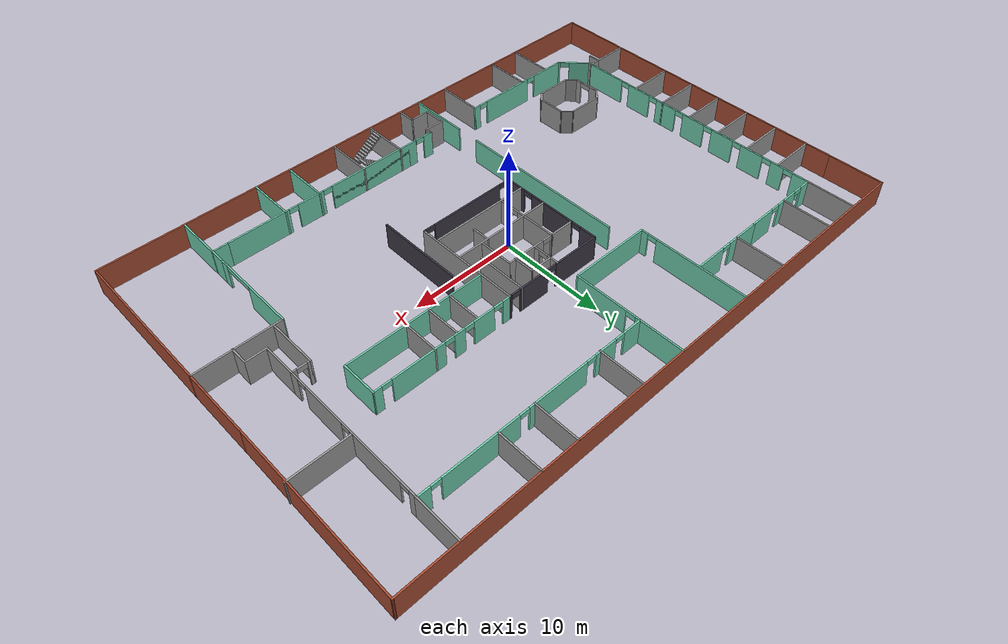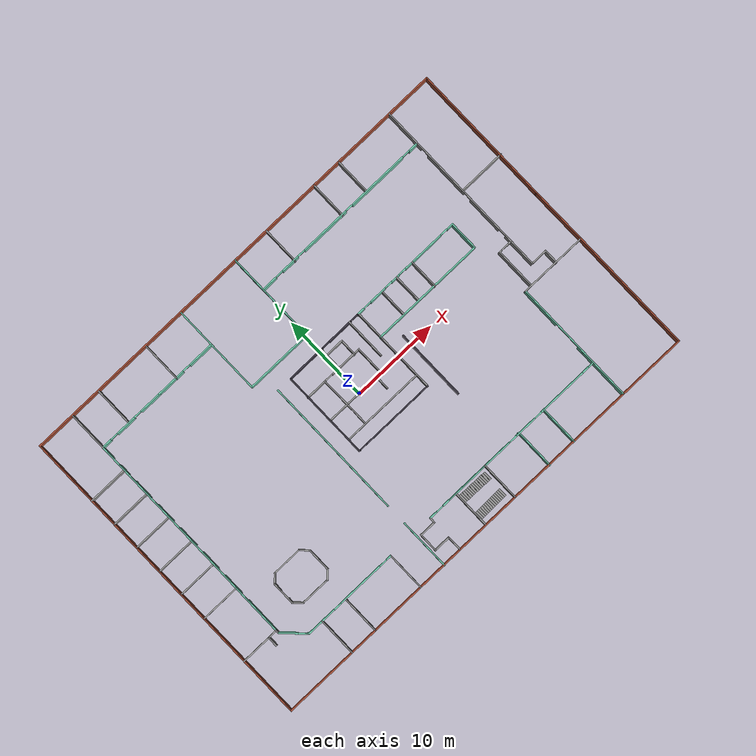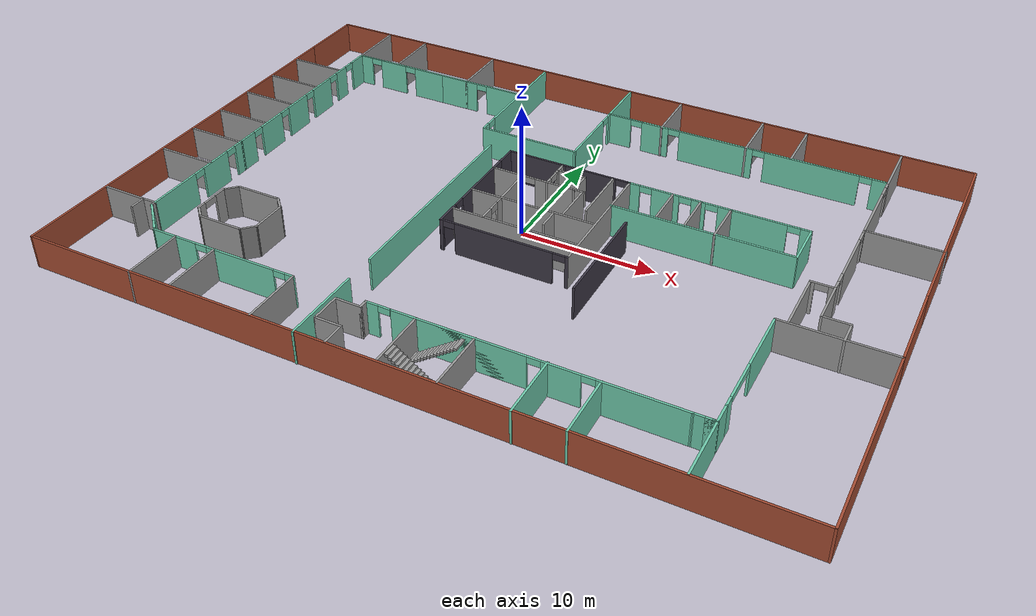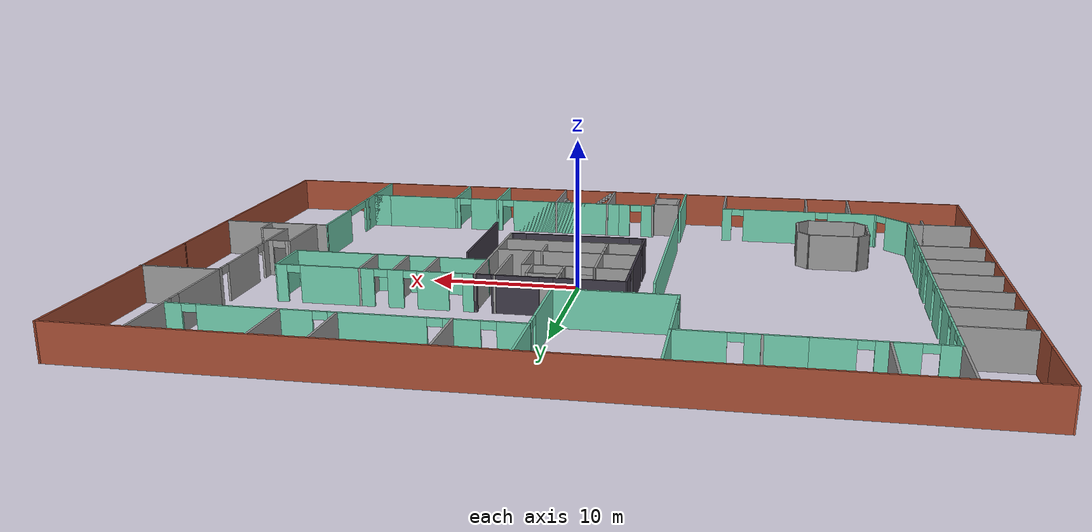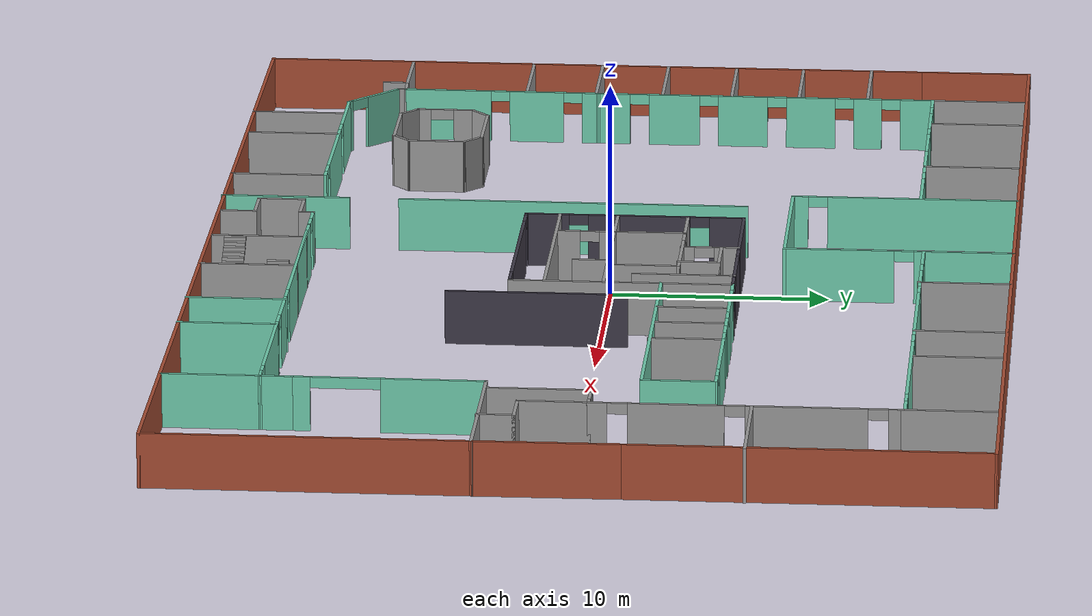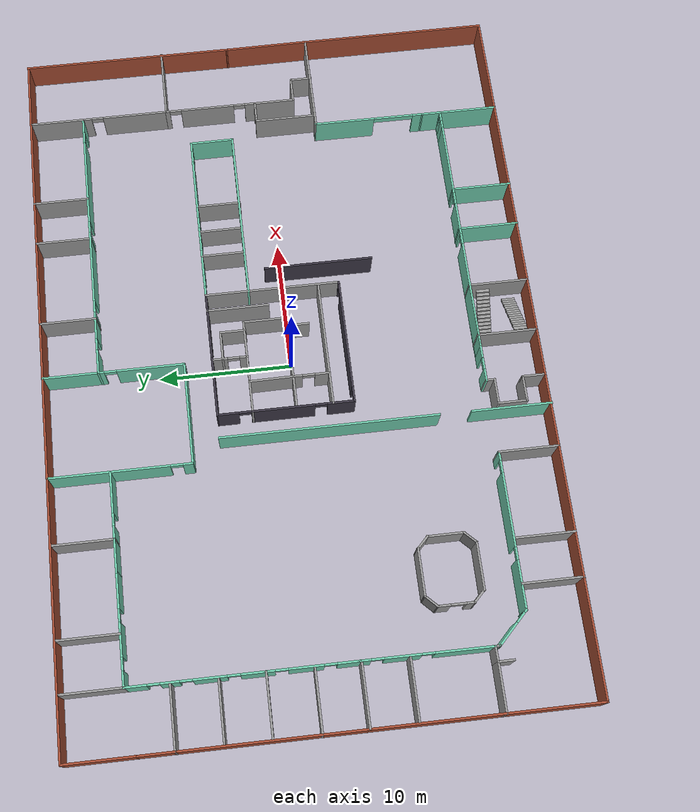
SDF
<?xml version='1.0'?>
<sdf version='1.7'>
  <model name='circuit_launch'>
    <pose>0.02205 -0.005269 0 0 -0 0</pose>
    <link name='Stairs_1'>
      <visual name='Stairs_1_Visual_0'>
        <pose>3.56304 -17.2142 0.083333 0 -0 -1.5708</pose>
        <geometry>
          <box>
            <size>1 0.233333 0.166667</size>
          </box>
        </geometry>
        <material>
          <script>
            <uri>file://media/materials/scripts/gazebo.material</uri>
            <name>Gazebo/Grey</name>
          </script>
          <ambient>1 1 1 1</ambient>
        </material>
        <meta>
          <layer>0</layer>
        </meta>
      </visual>
      <collision name='Stairs_1_Collision_0'>
        <geometry>
          <box>
            <size>1 0.233333 0.166667</size>
          </box>
        </geometry>
        <pose>3.56304 -17.2142 0.083333 0 -0 -1.5708</pose>
      </collision>
      <visual name='Stairs_1_Visual_1'>
        <pose>3.32971 -17.2142 0.25 0 -0 -1.5708</pose>
        <geometry>
          <box>
            <size>1 0.233333 0.166667</size>
          </box>
        </geometry>
        <material>
          <script>
            <uri>file://media/materials/scripts/gazebo.material</uri>
            <name>Gazebo/Grey</name>
          </script>
          <ambient>1 1 1 1</ambient>
        </material>
        <meta>
          <layer>0</layer>
        </meta>
      </visual>
      <collision name='Stairs_1_Collision_1'>
        <geometry>
          <box>
            <size>1 0.233333 0.166667</size>
          </box>
        </geometry>
        <pose>3.32971 -17.2142 0.25 0 -0 -1.5708</pose>
      </collision>
      <visual name='Stairs_1_Visual_2'>
        <pose>3.09638 -17.2142 0.416667 0 -0 -1.5708</pose>
        <geometry>
          <box>
            <size>1 0.233333 0.166667</size>
          </box>
        </geometry>
        <material>
          <script>
            <uri>file://media/materials/scripts/gazebo.material</uri>
            <name>Gazebo/Grey</name>
          </script>
          <ambient>1 1 1 1</ambient>
        </material>
        <meta>
          <layer>0</layer>
        </meta>
      </visual>
      <collision name='Stairs_1_Collision_2'>
        <geometry>
          <box>
            <size>1 0.233333 0.166667</size>
          </box>
        </geometry>
        <pose>3.09638 -17.2142 0.416667 0 -0 -1.5708</pose>
      </collision>
      <visual name='Stairs_1_Visual_3'>
        <pose>2.86304 -17.2142 0.583333 0 -0 -1.5708</pose>
        <geometry>
          <box>
            <size>1 0.233333 0.166667</size>
          </box>
        </geometry>
        <material>
          <script>
            <uri>file://media/materials/scripts/gazebo.material</uri>
            <name>Gazebo/Grey</name>
          </script>
          <ambient>1 1 1 1</ambient>
        </material>
        <meta>
          <layer>0</layer>
        </meta>
      </visual>
      <collision name='Stairs_1_Collision_3'>
        <geometry>
          <box>
            <size>1 0.233333 0.166667</size>
          </box>
        </geometry>
        <pose>2.86304 -17.2142 0.583333 0 -0 -1.5708</pose>
      </collision>
      <visual name='Stairs_1_Visual_4'>
        <pose>2.62971 -17.2142 0.75 0 -0 -1.5708</pose>
        <geometry>
          <box>
            <size>1 0.233333 0.166667</size>
          </box>
        </geometry>
        <material>
          <script>
            <uri>file://media/materials/scripts/gazebo.material</uri>
            <name>Gazebo/Grey</name>
          </script>
          <ambient>1 1 1 1</ambient>
        </material>
        <meta>
          <layer>0</layer>
        </meta>
      </visual>
      <collision name='Stairs_1_Collision_4'>
        <geometry>
          <box>
            <size>1 0.233333 0.166667</size>
          </box>
        </geometry>
        <pose>2.62971 -17.2142 0.75 0 -0 -1.5708</pose>
      </collision>
      <visual name='Stairs_1_Visual_5'>
        <pose>2.39638 -17.2142 0.916667 0 -0 -1.5708</pose>
        <geometry>
          <box>
            <size>1 0.233333 0.166667</size>
          </box>
        </geometry>
        <material>
          <script>
            <uri>file://media/materials/scripts/gazebo.material</uri>
            <name>Gazebo/Grey</name>
          </script>
          <ambient>1 1 1 1</ambient>
        </material>
        <meta>
          <layer>0</layer>
        </meta>
      </visual>
      <collision name='Stairs_1_Collision_5'>
        <geometry>
          <box>
            <size>1 0.233333 0.166667</size>
          </box>
        </geometry>
        <pose>2.39638 -17.2142 0.916667 0 -0 -1.5708</pose>
      </collision>
      <visual name='Stairs_1_Visual_6'>
        <pose>2.16304 -17.2142 1.08333 0 -0 -1.5708</pose>
        <geometry>
          <box>
            <size>1 0.233333 0.166667</size>
          </box>
        </geometry>
        <material>
          <script>
            <uri>file://media/materials/scripts/gazebo.material</uri>
            <name>Gazebo/Grey</name>
          </script>
          <ambient>1 1 1 1</ambient>
        </material>
        <meta>
          <layer>0</layer>
        </meta>
      </visual>
      <collision name='Stairs_1_Collision_6'>
        <geometry>
          <box>
            <size>1 0.233333 0.166667</size>
          </box>
        </geometry>
        <pose>2.16304 -17.2142 1.08333 0 -0 -1.5708</pose>
      </collision>
      <visual name='Stairs_1_Visual_7'>
        <pose>1.92971 -17.2142 1.25 0 -0 -1.5708</pose>
        <geometry>
          <box>
            <size>1 0.233333 0.166667</size>
          </box>
        </geometry>
        <material>
          <script>
            <uri>file://media/materials/scripts/gazebo.material</uri>
            <name>Gazebo/Grey</name>
          </script>
          <ambient>1 1 1 1</ambient>
        </material>
        <meta>
          <layer>0</layer>
        </meta>
      </visual>
      <collision name='Stairs_1_Collision_7'>
        <geometry>
          <box>
            <size>1 0.233333 0.166667</size>
          </box>
        </geometry>
        <pose>1.92971 -17.2142 1.25 0 -0 -1.5708</pose>
      </collision>
      <visual name='Stairs_1_Visual_8'>
        <pose>1.69638 -17.2142 1.41667 0 -0 -1.5708</pose>
        <geometry>
          <box>
            <size>1 0.233333 0.166667</size>
          </box>
        </geometry>
        <material>
          <script>
            <uri>file://media/materials/scripts/gazebo.material</uri>
            <name>Gazebo/Grey</name>
          </script>
          <ambient>1 1 1 1</ambient>
        </material>
        <meta>
          <layer>0</layer>
        </meta>
      </visual>
      <collision name='Stairs_1_Collision_8'>
        <geometry>
          <box>
            <size>1 0.233333 0.166667</size>
          </box>
        </geometry>
        <pose>1.69638 -17.2142 1.41667 0 -0 -1.5708</pose>
      </collision>
      <visual name='Stairs_1_Visual_9'>
        <pose>1.46304 -17.2142 1.58333 0 -0 -1.5708</pose>
        <geometry>
          <box>
            <size>1 0.233333 0.166667</size>
          </box>
        </geometry>
        <material>
          <script>
            <uri>file://media/materials/scripts/gazebo.material</uri>
            <name>Gazebo/Grey</name>
          </script>
          <ambient>1 1 1 1</ambient>
        </material>
        <meta>
          <layer>0</layer>
        </meta>
      </visual>
      <collision name='Stairs_1_Collision_9'>
        <geometry>
          <box>
            <size>1 0.233333 0.166667</size>
          </box>
        </geometry>
        <pose>1.46304 -17.2142 1.58333 0 -0 -1.5708</pose>
      </collision>
      <visual name='Stairs_1_Visual_10'>
        <pose>1.22971 -17.2142 1.75 0 -0 -1.5708</pose>
        <geometry>
          <box>
            <size>1 0.233333 0.166667</size>
          </box>
        </geometry>
        <material>
          <script>
            <uri>file://media/materials/scripts/gazebo.material</uri>
            <name>Gazebo/Grey</name>
          </script>
          <ambient>1 1 1 1</ambient>
        </material>
        <meta>
          <layer>0</layer>
        </meta>
      </visual>
      <collision name='Stairs_1_Collision_10'>
        <geometry>
          <box>
            <size>1 0.233333 0.166667</size>
          </box>
        </geometry>
        <pose>1.22971 -17.2142 1.75 0 -0 -1.5708</pose>
      </collision>
      <visual name='Stairs_1_Visual_11'>
        <pose>0.996375 -17.2142 1.91667 0 -0 -1.5708</pose>
        <geometry>
          <box>
            <size>1 0.233333 0.166667</size>
          </box>
        </geometry>
        <material>
          <script>
            <uri>file://media/materials/scripts/gazebo.material</uri>
            <name>Gazebo/Grey</name>
          </script>
          <ambient>1 1 1 1</ambient>
        </material>
        <meta>
          <layer>0</layer>
        </meta>
      </visual>
      <collision name='Stairs_1_Collision_11'>
        <geometry>
          <box>
            <size>1 0.233333 0.166667</size>
          </box>
        </geometry>
        <pose>0.996375 -17.2142 1.91667 0 -0 -1.5708</pose>
      </collision>
      <visual name='Stairs_1_Visual_12'>
        <pose>0.763042 -17.2142 2.08333 0 -0 -1.5708</pose>
        <geometry>
          <box>
            <size>1 0.233333 0.166667</size>
          </box>
        </geometry>
        <material>
          <script>
            <uri>file://media/materials/scripts/gazebo.material</uri>
            <name>Gazebo/Grey</name>
          </script>
          <ambient>1 1 1 1</ambient>
        </material>
        <meta>
          <layer>0</layer>
        </meta>
      </visual>
      <collision name='Stairs_1_Collision_12'>
        <geometry>
          <box>
            <size>1 0.233333 0.166667</size>
          </box>
        </geometry>
        <pose>0.763042 -17.2142 2.08333 0 -0 -1.5708</pose>
      </collision>
      <visual name='Stairs_1_Visual_13'>
        <pose>0.529709 -17.2142 2.25 0 -0 -1.5708</pose>
        <geometry>
          <box>
            <size>1 0.233333 0.166667</size>
          </box>
        </geometry>
        <material>
          <script>
            <uri>file://media/materials/scripts/gazebo.material</uri>
            <name>Gazebo/Grey</name>
          </script>
          <ambient>1 1 1 1</ambient>
        </material>
        <meta>
          <layer>0</layer>
        </meta>
      </visual>
      <collision name='Stairs_1_Collision_13'>
        <geometry>
          <box>
            <size>1 0.233333 0.166667</size>
          </box>
        </geometry>
        <pose>0.529709 -17.2142 2.25 0 -0 -1.5708</pose>
      </collision>
      <visual name='Stairs_1_Visual_14'>
        <pose>0.296375 -17.2142 2.41667 0 -0 -1.5708</pose>
        <geometry>
          <box>
            <size>1 0.233333 0.166667</size>
          </box>
        </geometry>
        <material>
          <script>
            <uri>file://media/materials/scripts/gazebo.material</uri>
            <name>Gazebo/Grey</name>
          </script>
          <ambient>1 1 1 1</ambient>
        </material>
        <meta>
          <layer>0</layer>
        </meta>
      </visual>
      <collision name='Stairs_1_Collision_14'>
        <geometry>
          <box>
            <size>1 0.233333 0.166667</size>
          </box>
        </geometry>
        <pose>0.296375 -17.2142 2.41667 0 -0 -1.5708</pose>
      </collision>
    </link>
    <link name='Stairs_2'>
      <visual name='Stairs_2_Visual_0'>
        <pose>0.290776 -14.8993 0.083333 0 -0 1.5708</pose>
        <geometry>
          <box>
            <size>1 0.233333 0.166667</size>
          </box>
        </geometry>
        <material>
          <script>
            <uri>file://media/materials/scripts/gazebo.material</uri>
            <name>Gazebo/Grey</name>
          </script>
          <ambient>1 1 1 1</ambient>
        </material>
        <meta>
          <layer>0</layer>
        </meta>
      </visual>
      <collision name='Stairs_2_Collision_0'>
        <geometry>
          <box>
            <size>1 0.233333 0.166667</size>
          </box>
        </geometry>
        <pose>0.290776 -14.8993 0.083333 0 -0 1.5708</pose>
      </collision>
      <visual name='Stairs_2_Visual_1'>
        <pose>0.524109 -14.8993 0.25 0 -0 1.5708</pose>
        <geometry>
          <box>
            <size>1 0.233333 0.166667</size>
          </box>
        </geometry>
        <material>
          <script>
            <uri>file://media/materials/scripts/gazebo.material</uri>
            <name>Gazebo/Grey</name>
          </script>
          <ambient>1 1 1 1</ambient>
        </material>
        <meta>
          <layer>0</layer>
        </meta>
      </visual>
      <collision name='Stairs_2_Collision_1'>
        <geometry>
          <box>
            <size>1 0.233333 0.166667</size>
          </box>
        </geometry>
        <pose>0.524109 -14.8993 0.25 0 -0 1.5708</pose>
      </collision>
      <visual name='Stairs_2_Visual_2'>
        <pose>0.757443 -14.8993 0.416667 0 -0 1.5708</pose>
        <geometry>
          <box>
            <size>1 0.233333 0.166667</size>
          </box>
        </geometry>
        <material>
          <script>
            <uri>file://media/materials/scripts/gazebo.material</uri>
            <name>Gazebo/Grey</name>
          </script>
          <ambient>1 1 1 1</ambient>
        </material>
        <meta>
          <layer>0</layer>
        </meta>
      </visual>
      <collision name='Stairs_2_Collision_2'>
        <geometry>
          <box>
            <size>1 0.233333 0.166667</size>
          </box>
        </geometry>
        <pose>0.757443 -14.8993 0.416667 0 -0 1.5708</pose>
      </collision>
      <visual name='Stairs_2_Visual_3'>
        <pose>0.990776 -14.8993 0.583333 0 -0 1.5708</pose>
        <geometry>
          <box>
            <size>1 0.233333 0.166667</size>
          </box>
        </geometry>
        <material>
          <script>
            <uri>file://media/materials/scripts/gazebo.material</uri>
            <name>Gazebo/Grey</name>
          </script>
          <ambient>1 1 1 1</ambient>
        </material>
        <meta>
          <layer>0</layer>
        </meta>
      </visual>
      <collision name='Stairs_2_Collision_3'>
        <geometry>
          <box>
            <size>1 0.233333 0.166667</size>
          </box>
        </geometry>
        <pose>0.990776 -14.8993 0.583333 0 -0 1.5708</pose>
      </collision>
      <visual name='Stairs_2_Visual_4'>
        <pose>1.22411 -14.8993 0.75 0 -0 1.5708</pose>
        <geometry>
          <box>
            <size>1 0.233333 0.166667</size>
          </box>
        </geometry>
        <material>
          <script>
            <uri>file://media/materials/scripts/gazebo.material</uri>
            <name>Gazebo/Grey</name>
          </script>
          <ambient>1 1 1 1</ambient>
        </material>
        <meta>
          <layer>0</layer>
        </meta>
      </visual>
      <collision name='Stairs_2_Collision_4'>
        <geometry>
          <box>
            <size>1 0.233333 0.166667</size>
          </box>
        </geometry>
        <pose>1.22411 -14.8993 0.75 0 -0 1.5708</pose>
      </collision>
      <visual name='Stairs_2_Visual_5'>
        <pose>1.45744 -14.8993 0.916667 0 -0 1.5708</pose>
        <geometry>
          <box>
            <size>1 0.233333 0.166667</size>
          </box>
        </geometry>
        <material>
          <script>
            <uri>file://media/materials/scripts/gazebo.material</uri>
            <name>Gazebo/Grey</name>
          </script>
          <ambient>1 1 1 1</ambient>
        </material>
        <meta>
          <layer>0</layer>
        </meta>
      </visual>
      <collision name='Stairs_2_Collision_5'>
        <geometry>
          <box>
            <size>1 0.233333 0.166667</size>
          </box>
        </geometry>
        <pose>1.45744 -14.8993 0.916667 0 -0 1.5708</pose>
      </collision>
      <visual name='Stairs_2_Visual_6'>
        <pose>1.69078 -14.8993 1.08333 0 -0 1.5708</pose>
        <geometry>
          <box>
            <size>1 0.233333 0.166667</size>
          </box>
        </geometry>
        <material>
          <script>
            <uri>file://media/materials/scripts/gazebo.material</uri>
            <name>Gazebo/Grey</name>
          </script>
          <ambient>1 1 1 1</ambient>
        </material>
        <meta>
          <layer>0</layer>
        </meta>
      </visual>
      <collision name='Stairs_2_Collision_6'>
        <geometry>
          <box>
            <size>1 0.233333 0.166667</size>
          </box>
        </geometry>
        <pose>1.69078 -14.8993 1.08333 0 -0 1.5708</pose>
      </collision>
      <visual name='Stairs_2_Visual_7'>
        <pose>1.92411 -14.8993 1.25 0 -0 1.5708</pose>
        <geometry>
          <box>
            <size>1 0.233333 0.166667</size>
          </box>
        </geometry>
        <material>
          <script>
            <uri>file://media/materials/scripts/gazebo.material</uri>
            <name>Gazebo/Grey</name>
          </script>
          <ambient>1 1 1 1</ambient>
        </material>
        <meta>
          <layer>0</layer>
        </meta>
      </visual>
      <collision name='Stairs_2_Collision_7'>
        <geometry>
          <box>
            <size>1 0.233333 0.166667</size>
          </box>
        </geometry>
        <pose>1.92411 -14.8993 1.25 0 -0 1.5708</pose>
      </collision>
      <visual name='Stairs_2_Visual_8'>
        <pose>2.15744 -14.8993 1.41667 0 -0 1.5708</pose>
        <geometry>
          <box>
            <size>1 0.233333 0.166667</size>
          </box>
        </geometry>
        <material>
          <script>
            <uri>file://media/materials/scripts/gazebo.material</uri>
            <name>Gazebo/Grey</name>
          </script>
          <ambient>1 1 1 1</ambient>
        </material>
        <meta>
          <layer>0</layer>
        </meta>
      </visual>
      <collision name='Stairs_2_Collision_8'>
        <geometry>
          <box>
            <size>1 0.233333 0.166667</size>
          </box>
        </geometry>
        <pose>2.15744 -14.8993 1.41667 0 -0 1.5708</pose>
      </collision>
      <visual name='Stairs_2_Visual_9'>
        <pose>2.39078 -14.8993 1.58333 0 -0 1.5708</pose>
        <geometry>
          <box>
            <size>1 0.233333 0.166667</size>
          </box>
        </geometry>
        <material>
          <script>
            <uri>file://media/materials/scripts/gazebo.material</uri>
            <name>Gazebo/Grey</name>
          </script>
          <ambient>1 1 1 1</ambient>
        </material>
        <meta>
          <layer>0</layer>
        </meta>
      </visual>
      <collision name='Stairs_2_Collision_9'>
        <geometry>
          <box>
            <size>1 0.233333 0.166667</size>
          </box>
        </geometry>
        <pose>2.39078 -14.8993 1.58333 0 -0 1.5708</pose>
      </collision>
      <visual name='Stairs_2_Visual_10'>
        <pose>2.62411 -14.8993 1.75 0 -0 1.5708</pose>
        <geometry>
          <box>
            <size>1 0.233333 0.166667</size>
          </box>
        </geometry>
        <material>
          <script>
            <uri>file://media/materials/scripts/gazebo.material</uri>
            <name>Gazebo/Grey</name>
          </script>
          <ambient>1 1 1 1</ambient>
        </material>
        <meta>
          <layer>0</layer>
        </meta>
      </visual>
      <collision name='Stairs_2_Collision_10'>
        <geometry>
          <box>
            <size>1 0.233333 0.166667</size>
          </box>
        </geometry>
        <pose>2.62411 -14.8993 1.75 0 -0 1.5708</pose>
      </collision>
      <visual name='Stairs_2_Visual_11'>
        <pose>2.85744 -14.8993 1.91667 0 -0 1.5708</pose>
        <geometry>
          <box>
            <size>1 0.233333 0.166667</size>
          </box>
        </geometry>
        <material>
          <script>
            <uri>file://media/materials/scripts/gazebo.material</uri>
            <name>Gazebo/Grey</name>
          </script>
          <ambient>1 1 1 1</ambient>
        </material>
        <meta>
          <layer>0</layer>
        </meta>
      </visual>
      <collision name='Stairs_2_Collision_11'>
        <geometry>
          <box>
            <size>1 0.233333 0.166667</size>
          </box>
        </geometry>
        <pose>2.85744 -14.8993 1.91667 0 -0 1.5708</pose>
      </collision>
      <visual name='Stairs_2_Visual_12'>
        <pose>3.09078 -14.8993 2.08333 0 -0 1.5708</pose>
        <geometry>
          <box>
            <size>1 0.233333 0.166667</size>
          </box>
        </geometry>
        <material>
          <script>
            <uri>file://media/materials/scripts/gazebo.material</uri>
            <name>Gazebo/Grey</name>
          </script>
          <ambient>1 1 1 1</ambient>
        </material>
        <meta>
          <layer>0</layer>
        </meta>
      </visual>
      <collision name='Stairs_2_Collision_12'>
        <geometry>
          <box>
            <size>1 0.233333 0.166667</size>
          </box>
        </geometry>
        <pose>3.09078 -14.8993 2.08333 0 -0 1.5708</pose>
      </collision>
      <visual name='Stairs_2_Visual_13'>
        <pose>3.32411 -14.8993 2.25 0 -0 1.5708</pose>
        <geometry>
          <box>
            <size>1 0.233333 0.166667</size>
          </box>
        </geometry>
        <material>
          <script>
            <uri>file://media/materials/scripts/gazebo.material</uri>
            <name>Gazebo/Grey</name>
          </script>
          <ambient>1 1 1 1</ambient>
        </material>
        <meta>
          <layer>0</layer>
        </meta>
      </visual>
      <collision name='Stairs_2_Collision_13'>
        <geometry>
          <box>
            <size>1 0.233333 0.166667</size>
          </box>
        </geometry>
        <pose>3.32411 -14.8993 2.25 0 -0 1.5708</pose>
      </collision>
      <visual name='Stairs_2_Visual_14'>
        <pose>3.55744 -14.8993 2.41667 0 -0 1.5708</pose>
        <geometry>
          <box>
            <size>1 0.233333 0.166667</size>
          </box>
        </geometry>
        <material>
          <script>
            <uri>file://media/materials/scripts/gazebo.material</uri>
            <name>Gazebo/Grey</name>
          </script>
          <ambient>1 1 1 1</ambient>
        </material>
        <meta>
          <layer>0</layer>
        </meta>
      </visual>
      <collision name='Stairs_2_Collision_14'>
        <geometry>
          <box>
            <size>1 0.233333 0.166667</size>
          </box>
        </geometry>
        <pose>3.55744 -14.8993 2.41667 0 -0 1.5708</pose>
      </collision>
    </link>
    <link name='Wall_100'>
      <pose>21.684 10.9599 0 0 -0 1.5708</pose>
      <visual name='Wall_100_Visual_0'>
        <pose>-0.787773 0 1.25 0 -0 0</pose>
        <geometry>
          <box>
            <size>5.12125 0.15 2.5</size>
          </box>
        </geometry>
        <material>
          <script>
            <uri>file://media/materials/scripts/gazebo.material</uri>
            <name>Gazebo/Grey</name>
          </script>
          <ambient>1 1 1 1</ambient>
        </material>
        <meta>
          <layer>0</layer>
        </meta>
      </visual>
      <collision name='Wall_100_Collision_0'>
        <geometry>
          <box>
            <size>5.12125 0.15 2.5</size>
          </box>
        </geometry>
        <pose>-0.787773 0 1.25 0 -0 0</pose>
      </collision>
      <visual name='Wall_100_Visual_1'>
        <pose>3.01063 0 1.25 0 -0 0</pose>
        <geometry>
          <box>
            <size>0.675545 0.15 2.5</size>
          </box>
        </geometry>
        <material>
          <script>
            <uri>file://media/materials/scripts/gazebo.material</uri>
            <name>Gazebo/Grey</name>
          </script>
          <ambient>1 1 1 1</ambient>
        </material>
        <meta>
          <layer>0</layer>
        </meta>
      </visual>
      <collision name='Wall_100_Collision_1'>
        <geometry>
          <box>
            <size>0.675545 0.15 2.5</size>
          </box>
        </geometry>
        <pose>3.01063 0 1.25 0 -0 0</pose>
      </collision>
      <visual name='Wall_100_Visual_2'>
        <pose>2.22286 0 2.25 0 -0 0</pose>
        <geometry>
          <box>
            <size>0.9 0.15 0.5</size>
          </box>
        </geometry>
        <material>
          <script>
            <uri>file://media/materials/scripts/gazebo.material</uri>
            <name>Gazebo/Grey</name>
          </script>
          <ambient>1 1 1 1</ambient>
        </material>
        <meta>
          <layer>0</layer>
        </meta>
      </visual>
      <collision name='Wall_100_Collision_2'>
        <geometry>
          <box>
            <size>0.9 0.15 0.5</size>
          </box>
        </geometry>
        <pose>2.22286 0 2.25 0 -0 0</pose>
      </collision>
    </link>
    <link name='Wall_107'>
      <pose>-18.6032 13.9124 0 0 -0 3.14159</pose>
      <visual name='Wall_107_Visual_0'>
        <pose>-2.69056 0 1.25 0 -0 0</pose>
        <geometry>
          <box>
            <size>2.61888 0.15 2.5</size>
          </box>
        </geometry>
        <material>
          <script>
            <uri>file://media/materials/scripts/gazebo.material</uri>
            <name>Gazebo/Grey</name>
          </script>
          <ambient>0.435294 0.796078 0.67451 1</ambient>
        </material>
        <meta>
          <layer>0</layer>
        </meta>
      </visual>
      <collision name='Wall_107_Collision_0'>
        <geometry>
          <box>
            <size>2.61888 0.15 2.5</size>
          </box>
        </geometry>
        <pose>-2.69056 0 1.25 0 -0 0</pose>
      </collision>
      <visual name='Wall_107_Visual_1'>
        <pose>0.710992 0 1.25 0 -0 0</pose>
        <geometry>
          <box>
            <size>2.38423 0.15 2.5</size>
          </box>
        </geometry>
        <material>
          <script>
            <uri>file://media/materials/scripts/gazebo.material</uri>
            <name>Gazebo/Grey</name>
          </script>
          <ambient>0.435294 0.796078 0.67451 1</ambient>
        </material>
        <meta>
          <layer>0</layer>
        </meta>
      </visual>
      <collision name='Wall_107_Collision_1'>
        <geometry>
          <box>
            <size>2.38423 0.15 2.5</size>
          </box>
        </geometry>
        <pose>0.710992 0 1.25 0 -0 0</pose>
      </collision>
      <visual name='Wall_107_Visual_2'>
        <pose>3.40155 0 1.25 0 -0 0</pose>
        <geometry>
          <box>
            <size>1.19689 0.15 2.5</size>
          </box>
        </geometry>
        <material>
          <script>
            <uri>file://media/materials/scripts/gazebo.material</uri>
            <name>Gazebo/Grey</name>
          </script>
          <ambient>0.435294 0.796078 0.67451 1</ambient>
        </material>
        <meta>
          <layer>0</layer>
        </meta>
      </visual>
      <collision name='Wall_107_Collision_2'>
        <geometry>
          <box>
            <size>1.19689 0.15 2.5</size>
          </box>
        </geometry>
        <pose>3.40155 0 1.25 0 -0 0</pose>
      </collision>
      <visual name='Wall_107_Visual_3'>
        <pose>-0.931122 0 2.25 0 -0 0</pose>
        <geometry>
          <box>
            <size>0.9 0.15 0.5</size>
          </box>
        </geometry>
        <material>
          <script>
            <uri>file://media/materials/scripts/gazebo.material</uri>
            <name>Gazebo/Grey</name>
          </script>
          <ambient>0.435294 0.796078 0.67451 1</ambient>
        </material>
        <meta>
          <layer>0</layer>
        </meta>
      </visual>
      <collision name='Wall_107_Collision_3'>
        <geometry>
          <box>
            <size>0.9 0.15 0.5</size>
          </box>
        </geometry>
        <pose>-0.931122 0 2.25 0 -0 0</pose>
      </collision>
      <visual name='Wall_107_Visual_4'>
        <pose>2.35311 0 2.25 0 -0 0</pose>
        <geometry>
          <box>
            <size>0.9 0.15 0.5</size>
          </box>
        </geometry>
        <material>
          <script>
            <uri>file://media/materials/scripts/gazebo.material</uri>
            <name>Gazebo/Grey</name>
          </script>
          <ambient>0.435294 0.796078 0.67451 1</ambient>
        </material>
        <meta>
          <layer>0</layer>
        </meta>
      </visual>
      <collision name='Wall_107_Collision_4'>
        <geometry>
          <box>
            <size>0.9 0.15 0.5</size>
          </box>
        </geometry>
        <pose>2.35311 0 2.25 0 -0 0</pose>
      </collision>
    </link>
    <link name='Wall_111'>
      <pose>-22.5282 5.86241 0 0 -0 -1.5708</pose>
      <visual name='Wall_111_Visual_0'>
        <pose>-7.31172 0 1.25 0 -0 0</pose>
        <geometry>
          <box>
            <size>1.62655 0.15 2.5</size>
          </box>
        </geometry>
        <material>
          <script>
            <uri>file://media/materials/scripts/gazebo.material</uri>
            <name>Gazebo/Grey</name>
          </script>
          <ambient>0.435294 0.796078 0.67451 1</ambient>
        </material>
        <meta>
          <layer>0</layer>
        </meta>
      </visual>
      <collision name='Wall_111_Collision_0'>
        <geometry>
          <box>
            <size>1.62655 0.15 2.5</size>
          </box>
        </geometry>
        <pose>-7.31172 0 1.25 0 -0 0</pose>
      </collision>
      <visual name='Wall_111_Visual_1'>
        <pose>-4.93124 0 1.25 0 -0 0</pose>
        <geometry>
          <box>
            <size>1.33442 0.15 2.5</size>
          </box>
        </geometry>
        <material>
          <script>
            <uri>file://media/materials/scripts/gazebo.material</uri>
            <name>Gazebo/Grey</name>
          </script>
          <ambient>0.435294 0.796078 0.67451 1</ambient>
        </material>
        <meta>
          <layer>0</layer>
        </meta>
      </visual>
      <collision name='Wall_111_Collision_1'>
        <geometry>
          <box>
            <size>1.33442 0.15 2.5</size>
          </box>
        </geometry>
        <pose>-4.93124 0 1.25 0 -0 0</pose>
      </collision>
      <visual name='Wall_111_Visual_2'>
        <pose>-2.19142 0 1.25 0 -0 0</pose>
        <geometry>
          <box>
            <size>2.34522 0.15 2.5</size>
          </box>
        </geometry>
        <material>
          <script>
            <uri>file://media/materials/scripts/gazebo.material</uri>
            <name>Gazebo/Grey</name>
          </script>
          <ambient>0.435294 0.796078 0.67451 1</ambient>
        </material>
        <meta>
          <layer>0</layer>
        </meta>
      </visual>
      <collision name='Wall_111_Collision_2'>
        <geometry>
          <box>
            <size>2.34522 0.15 2.5</size>
          </box>
        </geometry>
        <pose>-2.19142 0 1.25 0 -0 0</pose>
      </collision>
      <visual name='Wall_111_Visual_3'>
        <pose>1.0671 0 1.25 0 -0 0</pose>
        <geometry>
          <box>
            <size>2.37182 0.15 2.5</size>
          </box>
        </geometry>
        <material>
          <script>
            <uri>file://media/materials/scripts/gazebo.material</uri>
            <name>Gazebo/Grey</name>
          </script>
          <ambient>0.435294 0.796078 0.67451 1</ambient>
        </material>
        <meta>
          <layer>0</layer>
        </meta>
      </visual>
      <collision name='Wall_111_Collision_3'>
        <geometry>
          <box>
            <size>2.37182 0.15 2.5</size>
          </box>
        </geometry>
        <pose>1.0671 0 1.25 0 -0 0</pose>
      </collision>
      <visual name='Wall_111_Visual_4'>
        <pose>4.37883 0 1.25 0 -0 0</pose>
        <geometry>
          <box>
            <size>2.45162 0.15 2.5</size>
          </box>
        </geometry>
        <material>
          <script>
            <uri>file://media/materials/scripts/gazebo.material</uri>
            <name>Gazebo/Grey</name>
          </script>
          <ambient>0.435294 0.796078 0.67451 1</ambient>
        </material>
        <meta>
          <layer>0</layer>
        </meta>
      </visual>
      <collision name='Wall_111_Collision_4'>
        <geometry>
          <box>
            <size>2.45162 0.15 2.5</size>
          </box>
        </geometry>
        <pose>4.37883 0 1.25 0 -0 0</pose>
      </collision>
      <visual name='Wall_111_Visual_5'>
        <pose>7.31482 0 1.25 0 -0 0</pose>
        <geometry>
          <box>
            <size>1.62036 0.15 2.5</size>
          </box>
        </geometry>
        <material>
          <script>
            <uri>file://media/materials/scripts/gazebo.material</uri>
            <name>Gazebo/Grey</name>
          </script>
          <ambient>0.435294 0.796078 0.67451 1</ambient>
        </material>
        <meta>
          <layer>0</layer>
        </meta>
      </visual>
      <collision name='Wall_111_Collision_5'>
        <geometry>
          <box>
            <size>1.62036 0.15 2.5</size>
          </box>
        </geometry>
        <pose>7.31482 0 1.25 0 -0 0</pose>
      </collision>
      <visual name='Wall_111_Visual_6'>
        <pose>-6.04845 0 2.25 0 -0 0</pose>
        <geometry>
          <box>
            <size>0.9 0.15 0.5</size>
          </box>
        </geometry>
        <material>
          <script>
            <uri>file://media/materials/scripts/gazebo.material</uri>
            <name>Gazebo/Grey</name>
          </script>
          <ambient>0.435294 0.796078 0.67451 1</ambient>
        </material>
        <meta>
          <layer>0</layer>
        </meta>
      </visual>
      <collision name='Wall_111_Collision_6'>
        <geometry>
          <box>
            <size>0.9 0.15 0.5</size>
          </box>
        </geometry>
        <pose>-6.04845 0 2.25 0 -0 0</pose>
      </collision>
      <visual name='Wall_111_Visual_7'>
        <pose>-3.81403 0 2.25 0 -0 0</pose>
        <geometry>
          <box>
            <size>0.9 0.15 0.5</size>
          </box>
        </geometry>
        <material>
          <script>
            <uri>file://media/materials/scripts/gazebo.material</uri>
            <name>Gazebo/Grey</name>
          </script>
          <ambient>0.435294 0.796078 0.67451 1</ambient>
        </material>
        <meta>
          <layer>0</layer>
        </meta>
      </visual>
      <collision name='Wall_111_Collision_7'>
        <geometry>
          <box>
            <size>0.9 0.15 0.5</size>
          </box>
        </geometry>
        <pose>-3.81403 0 2.25 0 -0 0</pose>
      </collision>
      <visual name='Wall_111_Visual_8'>
        <pose>-0.568808 0 2.25 0 -0 0</pose>
        <geometry>
          <box>
            <size>0.9 0.15 0.5</size>
          </box>
        </geometry>
        <material>
          <script>
            <uri>file://media/materials/scripts/gazebo.material</uri>
            <name>Gazebo/Grey</name>
          </script>
          <ambient>0.435294 0.796078 0.67451 1</ambient>
        </material>
        <meta>
          <layer>0</layer>
        </meta>
      </visual>
      <collision name='Wall_111_Collision_8'>
        <geometry>
          <box>
            <size>0.9 0.15 0.5</size>
          </box>
        </geometry>
        <pose>-0.568808 0 2.25 0 -0 0</pose>
      </collision>
      <visual name='Wall_111_Visual_9'>
        <pose>2.70302 0 2.25 0 -0 0</pose>
        <geometry>
          <box>
            <size>0.9 0.15 0.5</size>
          </box>
        </geometry>
        <material>
          <script>
            <uri>file://media/materials/scripts/gazebo.material</uri>
            <name>Gazebo/Grey</name>
          </script>
          <ambient>0.435294 0.796078 0.67451 1</ambient>
        </material>
        <meta>
          <layer>0</layer>
        </meta>
      </visual>
      <collision name='Wall_111_Collision_9'>
        <geometry>
          <box>
            <size>0.9 0.15 0.5</size>
          </box>
        </geometry>
        <pose>2.70302 0 2.25 0 -0 0</pose>
      </collision>
      <visual name='Wall_111_Visual_10'>
        <pose>6.05464 0 2.25 0 -0 0</pose>
        <geometry>
          <box>
            <size>0.9 0.15 0.5</size>
          </box>
        </geometry>
        <material>
          <script>
            <uri>file://media/materials/scripts/gazebo.material</uri>
            <name>Gazebo/Grey</name>
          </script>
          <ambient>0.435294 0.796078 0.67451 1</ambient>
        </material>
        <meta>
          <layer>0</layer>
        </meta>
      </visual>
      <collision name='Wall_111_Collision_10'>
        <geometry>
          <box>
            <size>0.9 0.15 0.5</size>
          </box>
        </geometry>
        <pose>6.05464 0 2.25 0 -0 0</pose>
      </collision>
    </link>
    <link name='Wall_113'>
      <pose>-22.548 -6.83655 0 0 -0 -1.57507</pose>
      <visual name='Wall_113_Visual_0'>
        <pose>-4.29939 0 1.25 0 -0 0</pose>
        <geometry>
          <box>
            <size>0.849233 0.15 2.5</size>
          </box>
        </geometry>
        <material>
          <script>
            <uri>file://media/materials/scripts/gazebo.material</uri>
            <name>Gazebo/Grey</name>
          </script>
          <ambient>0.435294 0.796078 0.67451 1</ambient>
        </material>
        <meta>
          <layer>0</layer>
        </meta>
      </visual>
      <collision name='Wall_113_Collision_0'>
        <geometry>
          <box>
            <size>0.849233 0.15 2.5</size>
          </box>
        </geometry>
        <pose>-4.29939 0 1.25 0 -0 0</pose>
      </collision>
      <visual name='Wall_113_Visual_1'>
        <pose>-1.67683 0 1.25 0 -0 0</pose>
        <geometry>
          <box>
            <size>2.59588 0.15 2.5</size>
          </box>
        </geometry>
        <material>
          <script>
            <uri>file://media/materials/scripts/gazebo.material</uri>
            <name>Gazebo/Grey</name>
          </script>
          <ambient>0.435294 0.796078 0.67451 1</ambient>
        </material>
        <meta>
          <layer>0</layer>
        </meta>
      </visual>
      <collision name='Wall_113_Collision_1'>
        <geometry>
          <box>
            <size>2.59588 0.15 2.5</size>
          </box>
        </geometry>
        <pose>-1.67683 0 1.25 0 -0 0</pose>
      </collision>
      <visual name='Wall_113_Visual_2'>
        <pose>2.62255 0 1.25 0 -0 0</pose>
        <geometry>
          <box>
            <size>4.2029 0.15 2.5</size>
          </box>
        </geometry>
        <material>
          <script>
            <uri>file://media/materials/scripts/gazebo.material</uri>
            <name>Gazebo/Grey</name>
          </script>
          <ambient>0.435294 0.796078 0.67451 1</ambient>
        </material>
        <meta>
          <layer>0</layer>
        </meta>
      </visual>
      <collision name='Wall_113_Collision_2'>
        <geometry>
          <box>
            <size>4.2029 0.15 2.5</size>
          </box>
        </geometry>
        <pose>2.62255 0 1.25 0 -0 0</pose>
      </collision>
      <visual name='Wall_113_Visual_3'>
        <pose>-3.42477 0 2.25 0 -0 0</pose>
        <geometry>
          <box>
            <size>0.9 0.15 0.5</size>
          </box>
        </geometry>
        <material>
          <script>
            <uri>file://media/materials/scripts/gazebo.material</uri>
            <name>Gazebo/Grey</name>
          </script>
          <ambient>0.435294 0.796078 0.67451 1</ambient>
        </material>
        <meta>
          <layer>0</layer>
        </meta>
      </visual>
      <collision name='Wall_113_Collision_3'>
        <geometry>
          <box>
            <size>0.9 0.15 0.5</size>
          </box>
        </geometry>
        <pose>-3.42477 0 2.25 0 -0 0</pose>
      </collision>
      <visual name='Wall_113_Visual_4'>
        <pose>0.071105 0 2.25 0 -0 0</pose>
        <geometry>
          <box>
            <size>0.9 0.15 0.5</size>
          </box>
        </geometry>
        <material>
          <script>
            <uri>file://media/materials/scripts/gazebo.material</uri>
            <name>Gazebo/Grey</name>
          </script>
          <ambient>0.435294 0.796078 0.67451 1</ambient>
        </material>
        <meta>
          <layer>0</layer>
        </meta>
      </visual>
      <collision name='Wall_113_Collision_4'>
        <geometry>
          <box>
            <size>0.9 0.15 0.5</size>
          </box>
        </geometry>
        <pose>0.071105 0 2.25 0 -0 0</pose>
      </collision>
    </link>
    <link name='Wall_115'>
      <collision name='Wall_115_Collision'>
        <geometry>
          <box>
            <size>3.5 0.15 2.5</size>
          </box>
        </geometry>
        <pose>0 0 1.25 0 -0 0</pose>
      </collision>
      <visual name='Wall_115_Visual'>
        <pose>0 0 1.25 0 -0 0</pose>
        <geometry>
          <box>
            <size>3.5 0.15 2.5</size>
          </box>
        </geometry>
        <material>
          <script>
            <uri>file://media/materials/scripts/gazebo.material</uri>
            <name>Gazebo/Grey</name>
          </script>
          <ambient>1 1 1 1</ambient>
        </material>
        <meta>
          <layer>0</layer>
        </meta>
      </visual>
      <pose>-17.0124 -7.21468 0 0 -0 0</pose>
    </link>
    <link name='Wall_116'>
      <collision name='Wall_116_Collision'>
        <geometry>
          <box>
            <size>1.25 0.15 2.5</size>
          </box>
        </geometry>
        <pose>0 0 1.25 0 -0 0</pose>
      </collision>
      <visual name='Wall_116_Visual'>
        <pose>0 0 1.25 0 -0 0</pose>
        <geometry>
          <box>
            <size>1.25 0.15 2.5</size>
          </box>
        </geometry>
        <material>
          <script>
            <uri>file://media/materials/scripts/gazebo.material</uri>
            <name>Gazebo/Grey</name>
          </script>
          <ambient>1 1 1 1</ambient>
        </material>
        <meta>
          <layer>0</layer>
        </meta>
      </visual>
      <pose>-14.9485 -7.60359 0 0 -0 -0.785398</pose>
    </link>
    <link name='Wall_117'>
      <collision name='Wall_117_Collision'>
        <geometry>
          <box>
            <size>2.75 0.15 2.5</size>
          </box>
        </geometry>
        <pose>0 0 1.25 0 -0 0</pose>
      </collision>
      <visual name='Wall_117_Visual'>
        <pose>0 0 1.25 0 -0 0</pose>
        <geometry>
          <box>
            <size>2.75 0.15 2.5</size>
          </box>
        </geometry>
        <material>
          <script>
            <uri>file://media/materials/scripts/gazebo.material</uri>
            <name>Gazebo/Grey</name>
          </script>
          <ambient>1 1 1 1</ambient>
        </material>
        <meta>
          <layer>0</layer>
        </meta>
      </visual>
      <pose>-14.5595 -9.2925 0 0 -0 -1.5708</pose>
    </link>
    <link name='Wall_118'>
      <collision name='Wall_118_Collision'>
        <geometry>
          <box>
            <size>1.25 0.15 2.5</size>
          </box>
        </geometry>
        <pose>0 0 1.25 0 -0 0</pose>
      </collision>
      <visual name='Wall_118_Visual'>
        <pose>0 0 1.25 0 -0 0</pose>
        <geometry>
          <box>
            <size>1.25 0.15 2.5</size>
          </box>
        </geometry>
        <material>
          <script>
            <uri>file://media/materials/scripts/gazebo.material</uri>
            <name>Gazebo/Grey</name>
          </script>
          <ambient>1 1 1 1</ambient>
        </material>
        <meta>
          <layer>0</layer>
        </meta>
      </visual>
      <pose>-14.9485 -10.9814 0 0 -0 -2.35619</pose>
    </link>
    <link name='Wall_119'>
      <collision name='Wall_119_Collision'>
        <geometry>
          <box>
            <size>3.5 0.15 2.5</size>
          </box>
        </geometry>
        <pose>0 0 1.25 0 -0 0</pose>
      </collision>
      <visual name='Wall_119_Visual'>
        <pose>0 0 1.25 0 -0 0</pose>
        <geometry>
          <box>
            <size>3.5 0.15 2.5</size>
          </box>
        </geometry>
        <material>
          <script>
            <uri>file://media/materials/scripts/gazebo.material</uri>
            <name>Gazebo/Grey</name>
          </script>
          <ambient>1 1 1 1</ambient>
        </material>
        <meta>
          <layer>0</layer>
        </meta>
      </visual>
      <pose>-17.0124 -11.3703 0 0 -0 3.14159</pose>
    </link>
    <link name='Wall_12'>
      <collision name='Wall_12_Collision'>
        <geometry>
          <box>
            <size>10.25 0.15 2.5</size>
          </box>
        </geometry>
        <pose>0 0 1.25 0 -0 0</pose>
      </collision>
      <visual name='Wall_12_Visual'>
        <pose>0 0 1.25 0 -0 0</pose>
        <geometry>
          <box>
            <size>10.25 0.15 2.5</size>
          </box>
        </geometry>
        <material>
          <script>
            <uri>file://media/materials/scripts/gazebo.material</uri>
            <name>Gazebo/Grey</name>
          </script>
          <ambient>1 1 1 1</ambient>
        </material>
        <meta>
          <layer>0</layer>
        </meta>
      </visual>
      <pose>5.48338 0.868521 0 0 -0 1.5708</pose>
    </link>
    <link name='Wall_120'>
      <collision name='Wall_120_Collision'>
        <geometry>
          <box>
            <size>1.25 0.15 2.5</size>
          </box>
        </geometry>
        <pose>0 0 1.25 0 -0 0</pose>
      </collision>
      <visual name='Wall_120_Visual'>
        <pose>0 0 1.25 0 -0 0</pose>
        <geometry>
          <box>
            <size>1.25 0.15 2.5</size>
          </box>
        </geometry>
        <material>
          <script>
            <uri>file://media/materials/scripts/gazebo.material</uri>
            <name>Gazebo/Grey</name>
          </script>
          <ambient>1 1 1 1</ambient>
        </material>
        <meta>
          <layer>0</layer>
        </meta>
      </visual>
      <pose>-19.0763 -10.9814 0 0 -0 2.35619</pose>
    </link>
    <link name='Wall_121'>
      <pose>-19.4652 -9.2925 0 0 -0 1.5708</pose>
      <visual name='Wall_121_Visual_0'>
        <pose>-1.04498 0 1.25 0 -0 0</pose>
        <geometry>
          <box>
            <size>0.66004 0.15 2.5</size>
          </box>
        </geometry>
        <material>
          <script>
            <uri>file://media/materials/scripts/gazebo.material</uri>
            <name>Gazebo/Grey</name>
          </script>
          <ambient>1 1 1 1</ambient>
        </material>
        <meta>
          <layer>0</layer>
        </meta>
      </visual>
      <collision name='Wall_121_Collision_0'>
        <geometry>
          <box>
            <size>0.66004 0.15 2.5</size>
          </box>
        </geometry>
        <pose>-1.04498 0 1.25 0 -0 0</pose>
      </collision>
      <visual name='Wall_121_Visual_1'>
        <pose>0.884108 0 1.25 0 -0 0</pose>
        <geometry>
          <box>
            <size>0.981785 0.15 2.5</size>
          </box>
        </geometry>
        <material>
          <script>
            <uri>file://media/materials/scripts/gazebo.material</uri>
            <name>Gazebo/Grey</name>
          </script>
          <ambient>1 1 1 1</ambient>
        </material>
        <meta>
          <layer>0</layer>
        </meta>
      </visual>
      <collision name='Wall_121_Collision_1'>
        <geometry>
          <box>
            <size>0.981785 0.15 2.5</size>
          </box>
        </geometry>
        <pose>0.884108 0 1.25 0 -0 0</pose>
      </collision>
      <visual name='Wall_121_Visual_2'>
        <pose>-0.160872 0 2.25 0 -0 0</pose>
        <geometry>
          <box>
            <size>1.10817 0.15 0.5</size>
          </box>
        </geometry>
        <material>
          <script>
            <uri>file://media/materials/scripts/gazebo.material</uri>
            <name>Gazebo/Grey</name>
          </script>
          <ambient>1 1 1 1</ambient>
        </material>
        <meta>
          <layer>0</layer>
        </meta>
      </visual>
      <collision name='Wall_121_Collision_2'>
        <geometry>
          <box>
            <size>1.10817 0.15 0.5</size>
          </box>
        </geometry>
        <pose>-0.160872 0 2.25 0 -0 0</pose>
      </collision>
    </link>
    <link name='Wall_122'>
      <collision name='Wall_122_Collision'>
        <geometry>
          <box>
            <size>1.25 0.15 2.5</size>
          </box>
        </geometry>
        <pose>0 0 1.25 0 -0 0</pose>
      </collision>
      <visual name='Wall_122_Visual'>
        <pose>0 0 1.25 0 -0 0</pose>
        <geometry>
          <box>
            <size>1.25 0.15 2.5</size>
          </box>
        </geometry>
        <material>
          <script>
            <uri>file://media/materials/scripts/gazebo.material</uri>
            <name>Gazebo/Grey</name>
          </script>
          <ambient>1 1 1 1</ambient>
        </material>
        <meta>
          <layer>0</layer>
        </meta>
      </visual>
      <pose>-19.0763 -7.60359 0 0 -0 0.785398</pose>
    </link>
    <link name='Wall_124'>
      <collision name='Wall_124_Collision'>
        <geometry>
          <box>
            <size>16.25 0.15 2.5</size>
          </box>
        </geometry>
        <pose>0 0 1.25 0 -0 0</pose>
      </collision>
      <visual name='Wall_124_Visual'>
        <pose>0 0 1.25 0 -0 0</pose>
        <geometry>
          <box>
            <size>16.25 0.15 2.5</size>
          </box>
        </geometry>
        <material>
          <script>
            <uri>file://media/materials/scripts/gazebo.material</uri>
            <name>Gazebo/Grey</name>
          </script>
          <ambient>0.435294 0.796078 0.67451 1</ambient>
        </material>
        <meta>
          <layer>0</layer>
        </meta>
      </visual>
      <pose>-5.75967 -2.14165 0 0 -0 -1.5708</pose>
    </link>
    <link name='Wall_126'>
      <collision name='Wall_126_Collision'>
        <geometry>
          <box>
            <size>6 0.15 2.5</size>
          </box>
        </geometry>
        <pose>0 0 1.25 0 -0 0</pose>
      </collision>
      <visual name='Wall_126_Visual'>
        <pose>0 0 1.25 0 -0 0</pose>
        <geometry>
          <box>
            <size>6 0.15 2.5</size>
          </box>
        </geometry>
        <material>
          <script>
            <uri>file://media/materials/scripts/gazebo.material</uri>
            <name>Gazebo/Grey</name>
          </script>
          <ambient>0.435294 0.796078 0.67451 1</ambient>
        </material>
        <meta>
          <layer>0</layer>
        </meta>
      </visual>
      <pose>-5.76615 -15.5406 0 0 -0 -1.5708</pose>
    </link>
    <link name='Wall_13'>
      <pose>0.725889 5.90411 0 0 -0 -3.13856</pose>
      <visual name='Wall_13_Visual_0'>
        <pose>-4.71281 0 1.25 0 -0 0</pose>
        <geometry>
          <box>
            <size>0.239451 0.15 2.5</size>
          </box>
        </geometry>
        <material>
          <script>
            <uri>file://media/materials/scripts/gazebo.material</uri>
            <name>Gazebo/Grey</name>
          </script>
          <ambient>0.239216 0.219608 0.27451 1</ambient>
        </material>
        <meta>
          <layer>0</layer>
        </meta>
      </visual>
      <collision name='Wall_13_Collision_0'>
        <geometry>
          <box>
            <size>0.239451 0.15 2.5</size>
          </box>
        </geometry>
        <pose>-4.71281 0 1.25 0 -0 0</pose>
      </collision>
      <visual name='Wall_13_Visual_1'>
        <pose>-2.18096 0 1.25 0 -0 0</pose>
        <geometry>
          <box>
            <size>3.02425 0.15 2.5</size>
          </box>
        </geometry>
        <material>
          <script>
            <uri>file://media/materials/scripts/gazebo.material</uri>
            <name>Gazebo/Grey</name>
          </script>
          <ambient>0.239216 0.219608 0.27451 1</ambient>
        </material>
        <meta>
          <layer>0</layer>
        </meta>
      </visual>
      <collision name='Wall_13_Collision_1'>
        <geometry>
          <box>
            <size>3.02425 0.15 2.5</size>
          </box>
        </geometry>
        <pose>-2.18096 0 1.25 0 -0 0</pose>
      </collision>
      <visual name='Wall_13_Visual_2'>
        <pose>2.53185 0 1.25 0 -0 0</pose>
        <geometry>
          <box>
            <size>4.60137 0.15 2.5</size>
          </box>
        </geometry>
        <material>
          <script>
            <uri>file://media/materials/scripts/gazebo.material</uri>
            <name>Gazebo/Grey</name>
          </script>
          <ambient>0.239216 0.219608 0.27451 1</ambient>
        </material>
        <meta>
          <layer>0</layer>
        </meta>
      </visual>
      <collision name='Wall_13_Collision_2'>
        <geometry>
          <box>
            <size>4.60137 0.15 2.5</size>
          </box>
        </geometry>
        <pose>2.53185 0 1.25 0 -0 0</pose>
      </collision>
      <visual name='Wall_13_Visual_3'>
        <pose>-4.14309 0 2.25 0 -0 0</pose>
        <geometry>
          <box>
            <size>0.9 0.15 0.5</size>
          </box>
        </geometry>
        <material>
          <script>
            <uri>file://media/materials/scripts/gazebo.material</uri>
            <name>Gazebo/Grey</name>
          </script>
          <ambient>0.239216 0.219608 0.27451 1</ambient>
        </material>
        <meta>
          <layer>0</layer>
        </meta>
      </visual>
      <collision name='Wall_13_Collision_3'>
        <geometry>
          <box>
            <size>0.9 0.15 0.5</size>
          </box>
        </geometry>
        <pose>-4.14309 0 2.25 0 -0 0</pose>
      </collision>
      <visual name='Wall_13_Visual_4'>
        <pose>-0.218831 0 2.25 0 -0 0</pose>
        <geometry>
          <box>
            <size>0.9 0.15 0.5</size>
          </box>
        </geometry>
        <material>
          <script>
            <uri>file://media/materials/scripts/gazebo.material</uri>
            <name>Gazebo/Grey</name>
          </script>
          <ambient>0.239216 0.219608 0.27451 1</ambient>
        </material>
        <meta>
          <layer>0</layer>
        </meta>
      </visual>
      <collision name='Wall_13_Collision_4'>
        <geometry>
          <box>
            <size>0.9 0.15 0.5</size>
          </box>
        </geometry>
        <pose>-0.218831 0 2.25 0 -0 0</pose>
      </collision>
    </link>
    <link name='Wall_135'>
      <collision name='Wall_135_Collision'>
        <geometry>
          <box>
            <size>3.25 0.15 2.5</size>
          </box>
        </geometry>
        <pose>0 0 1.25 0 -0 0</pose>
      </collision>
      <visual name='Wall_135_Visual'>
        <pose>0 0 1.25 0 -0 0</pose>
        <geometry>
          <box>
            <size>3.25 0.15 2.5</size>
          </box>
        </geometry>
        <material>
          <script>
            <uri>file://media/materials/scripts/gazebo.material</uri>
            <name>Gazebo/Grey</name>
          </script>
          <ambient>1 1 1 1</ambient>
        </material>
        <meta>
          <layer>0</layer>
        </meta>
      </visual>
      <pose>21.684 -0.963464 0 0 -0 -1.5708</pose>
    </link>
    <link name='Wall_136'>
      <collision name='Wall_136_Collision'>
        <geometry>
          <box>
            <size>2 0.15 2.5</size>
          </box>
        </geometry>
        <pose>0 0 1.25 0 -0 0</pose>
      </collision>
      <visual name='Wall_136_Visual'>
        <pose>0 0 1.25 0 -0 0</pose>
        <geometry>
          <box>
            <size>2 0.15 2.5</size>
          </box>
        </geometry>
        <material>
          <script>
            <uri>file://media/materials/scripts/gazebo.material</uri>
            <name>Gazebo/Grey</name>
          </script>
          <ambient>1 1 1 1</ambient>
        </material>
        <meta>
          <layer>0</layer>
        </meta>
      </visual>
      <pose>22.609 -2.51346 0 0 -0 0</pose>
    </link>
    <link name='Wall_137'>
      <collision name='Wall_137_Collision'>
        <geometry>
          <box>
            <size>1.75 0.15 2.5</size>
          </box>
        </geometry>
        <pose>0 0 1.25 0 -0 0</pose>
      </collision>
      <visual name='Wall_137_Visual'>
        <pose>0 0 1.25 0 -0 0</pose>
        <geometry>
          <box>
            <size>1.75 0.15 2.5</size>
          </box>
        </geometry>
        <material>
          <script>
            <uri>file://media/materials/scripts/gazebo.material</uri>
            <name>Gazebo/Grey</name>
          </script>
          <ambient>1 1 1 1</ambient>
        </material>
        <meta>
          <layer>0</layer>
        </meta>
      </visual>
      <pose>23.534 -3.31346 0 0 -0 -1.5708</pose>
    </link>
    <link name='Wall_139'>
      <collision name='Wall_139_Collision'>
        <geometry>
          <box>
            <size>0.75 0.15 2.5</size>
          </box>
        </geometry>
        <pose>0 0 1.25 0 -0 0</pose>
      </collision>
      <visual name='Wall_139_Visual'>
        <pose>0 0 1.25 0 -0 0</pose>
        <geometry>
          <box>
            <size>0.75 0.15 2.5</size>
          </box>
        </geometry>
        <material>
          <script>
            <uri>file://media/materials/scripts/gazebo.material</uri>
            <name>Gazebo/Grey</name>
          </script>
          <ambient>1 1 1 1</ambient>
        </material>
        <meta>
          <layer>0</layer>
        </meta>
      </visual>
      <pose>-3.52583 -14.3275 0 0 -0 -1.5708</pose>
    </link>
    <link name='Wall_14'>
      <pose>-4.03141 0.854113 0 0 -0 -1.57076</pose>
      <visual name='Wall_14_Visual_0'>
        <pose>-4.27972 0 1.25 0 -0 0</pose>
        <geometry>
          <box>
            <size>1.66175 0.15 2.5</size>
          </box>
        </geometry>
        <material>
          <script>
            <uri>file://media/materials/scripts/gazebo.material</uri>
            <name>Gazebo/Grey</name>
          </script>
          <ambient>0.239216 0.219608 0.27451 1</ambient>
        </material>
        <meta>
          <layer>0</layer>
        </meta>
      </visual>
      <collision name='Wall_14_Collision_0'>
        <geometry>
          <box>
            <size>1.66175 0.15 2.5</size>
          </box>
        </geometry>
        <pose>-4.27972 0 1.25 0 -0 0</pose>
      </collision>
      <visual name='Wall_14_Visual_1'>
        <pose>-0.200437 0 1.25 0 -0 0</pose>
        <geometry>
          <box>
            <size>4.69681 0.15 2.5</size>
          </box>
        </geometry>
        <material>
          <script>
            <uri>file://media/materials/scripts/gazebo.material</uri>
            <name>Gazebo/Grey</name>
          </script>
          <ambient>0.239216 0.219608 0.27451 1</ambient>
        </material>
        <meta>
          <layer>0</layer>
        </meta>
      </visual>
      <collision name='Wall_14_Collision_1'>
        <geometry>
          <box>
            <size>4.69681 0.15 2.5</size>
          </box>
        </geometry>
        <pose>-0.200437 0 1.25 0 -0 0</pose>
      </collision>
      <visual name='Wall_14_Visual_2'>
        <pose>4.07928 0 1.25 0 -0 0</pose>
        <geometry>
          <box>
            <size>2.06262 0.15 2.5</size>
          </box>
        </geometry>
        <material>
          <script>
            <uri>file://media/materials/scripts/gazebo.material</uri>
            <name>Gazebo/Grey</name>
          </script>
          <ambient>0.239216 0.219608 0.27451 1</ambient>
        </material>
        <meta>
          <layer>0</layer>
        </meta>
      </visual>
      <collision name='Wall_14_Collision_2'>
        <geometry>
          <box>
            <size>2.06262 0.15 2.5</size>
          </box>
        </geometry>
        <pose>4.07928 0 1.25 0 -0 0</pose>
      </collision>
      <visual name='Wall_14_Visual_3'>
        <pose>-2.99884 0 2.25 0 -0 0</pose>
        <geometry>
          <box>
            <size>0.9 0.15 0.5</size>
          </box>
        </geometry>
        <material>
          <script>
            <uri>file://media/materials/scripts/gazebo.material</uri>
            <name>Gazebo/Grey</name>
          </script>
          <ambient>0.239216 0.219608 0.27451 1</ambient>
        </material>
        <meta>
          <layer>0</layer>
        </meta>
      </visual>
      <collision name='Wall_14_Collision_3'>
        <geometry>
          <box>
            <size>0.9 0.15 0.5</size>
          </box>
        </geometry>
        <pose>-2.99884 0 2.25 0 -0 0</pose>
      </collision>
      <visual name='Wall_14_Visual_4'>
        <pose>2.59797 0 2.25 0 -0 0</pose>
        <geometry>
          <box>
            <size>0.9 0.15 0.5</size>
          </box>
        </geometry>
        <material>
          <script>
            <uri>file://media/materials/scripts/gazebo.material</uri>
            <name>Gazebo/Grey</name>
          </script>
          <ambient>0.239216 0.219608 0.27451 1</ambient>
        </material>
        <meta>
          <layer>0</layer>
        </meta>
      </visual>
      <collision name='Wall_14_Collision_4'>
        <geometry>
          <box>
            <size>0.9 0.15 0.5</size>
          </box>
        </geometry>
        <pose>2.59797 0 2.25 0 -0 0</pose>
      </collision>
    </link>
    <link name='Wall_140'>
      <collision name='Wall_140_Collision'>
        <geometry>
          <box>
            <size>2 0.15 2.5</size>
          </box>
        </geometry>
        <pose>0 0 1.25 0 -0 0</pose>
      </collision>
      <visual name='Wall_140_Visual'>
        <pose>0 0 1.25 0 -0 0</pose>
        <geometry>
          <box>
            <size>2 0.15 2.5</size>
          </box>
        </geometry>
        <material>
          <script>
            <uri>file://media/materials/scripts/gazebo.material</uri>
            <name>Gazebo/Grey</name>
          </script>
          <ambient>1 1 1 1</ambient>
        </material>
        <meta>
          <layer>0</layer>
        </meta>
      </visual>
      <pose>-4.45083 -14.6275 0 0 -0 3.14159</pose>
    </link>
    <link name='Wall_141'>
      <collision name='Wall_141_Collision'>
        <geometry>
          <box>
            <size>2.25 0.15 2.5</size>
          </box>
        </geometry>
        <pose>0 0 1.25 0 -0 0</pose>
      </collision>
      <visual name='Wall_141_Visual'>
        <pose>0 0 1.25 0 -0 0</pose>
        <geometry>
          <box>
            <size>2.25 0.15 2.5</size>
          </box>
        </geometry>
        <material>
          <script>
            <uri>file://media/materials/scripts/gazebo.material</uri>
            <name>Gazebo/Grey</name>
          </script>
          <ambient>1 1 1 1</ambient>
        </material>
        <meta>
          <layer>0</layer>
        </meta>
      </visual>
      <pose>-5.37583 -15.6775 0 0 -0 -1.5708</pose>
    </link>
    <link name='Wall_142'>
      <collision name='Wall_142_Collision'>
        <geometry>
          <box>
            <size>2 0.15 2.5</size>
          </box>
        </geometry>
        <pose>0 0 1.25 0 -0 0</pose>
      </collision>
      <visual name='Wall_142_Visual'>
        <pose>0 0 1.25 0 -0 0</pose>
        <geometry>
          <box>
            <size>2 0.15 2.5</size>
          </box>
        </geometry>
        <material>
          <script>
            <uri>file://media/materials/scripts/gazebo.material</uri>
            <name>Gazebo/Grey</name>
          </script>
          <ambient>1 1 1 1</ambient>
        </material>
        <meta>
          <layer>0</layer>
        </meta>
      </visual>
      <pose>-4.45083 -16.7275 0 0 -0 0</pose>
    </link>
    <link name='Wall_144'>
      <collision name='Wall_144_Collision'>
        <geometry>
          <box>
            <size>1.75 0.15 2.5</size>
          </box>
        </geometry>
        <pose>0 0 1.25 0 -0 0</pose>
      </collision>
      <visual name='Wall_144_Visual'>
        <pose>0 0 1.25 0 -0 0</pose>
        <geometry>
          <box>
            <size>1.75 0.15 2.5</size>
          </box>
        </geometry>
        <material>
          <script>
            <uri>file://media/materials/scripts/gazebo.material</uri>
            <name>Gazebo/Grey</name>
          </script>
          <ambient>1 1 1 1</ambient>
        </material>
        <meta>
          <layer>0</layer>
        </meta>
      </visual>
      <pose>-3.52583 -17.5275 0 0 -0 -1.5708</pose>
    </link>
    <link name='Wall_146'>
      <pose>-14.7008 -14.0275 0 0 -0 0</pose>
      <visual name='Wall_146_Visual_0'>
        <pose>-3.95927 0 1.25 0 -0 0</pose>
        <geometry>
          <box>
            <size>3.58146 0.15 2.5</size>
          </box>
        </geometry>
        <material>
          <script>
            <uri>file://media/materials/scripts/gazebo.material</uri>
            <name>Gazebo/Grey</name>
          </script>
          <ambient>0.435294 0.796078 0.67451 1</ambient>
        </material>
        <meta>
          <layer>0</layer>
        </meta>
      </visual>
      <collision name='Wall_146_Collision_0'>
        <geometry>
          <box>
            <size>3.58146 0.15 2.5</size>
          </box>
        </geometry>
        <pose>-3.95927 0 1.25 0 -0 0</pose>
      </collision>
      <visual name='Wall_146_Visual_1'>
        <pose>1.43879 0 1.25 0 -0 0</pose>
        <geometry>
          <box>
            <size>5.41466 0.15 2.5</size>
          </box>
        </geometry>
        <material>
          <script>
            <uri>file://media/materials/scripts/gazebo.material</uri>
            <name>Gazebo/Grey</name>
          </script>
          <ambient>0.435294 0.796078 0.67451 1</ambient>
        </material>
        <meta>
          <layer>0</layer>
        </meta>
      </visual>
      <collision name='Wall_146_Collision_1'>
        <geometry>
          <box>
            <size>5.41466 0.15 2.5</size>
          </box>
        </geometry>
        <pose>1.43879 0 1.25 0 -0 0</pose>
      </collision>
      <visual name='Wall_146_Visual_2'>
        <pose>5.39806 0 1.25 0 -0 0</pose>
        <geometry>
          <box>
            <size>0.703885 0.15 2.5</size>
          </box>
        </geometry>
        <material>
          <script>
            <uri>file://media/materials/scripts/gazebo.material</uri>
            <name>Gazebo/Grey</name>
          </script>
          <ambient>0.435294 0.796078 0.67451 1</ambient>
        </material>
        <meta>
          <layer>0</layer>
        </meta>
      </visual>
      <collision name='Wall_146_Collision_2'>
        <geometry>
          <box>
            <size>0.703885 0.15 2.5</size>
          </box>
        </geometry>
        <pose>5.39806 0 1.25 0 -0 0</pose>
      </collision>
      <visual name='Wall_146_Visual_3'>
        <pose>-1.71854 0 2.25 0 -0 0</pose>
        <geometry>
          <box>
            <size>0.9 0.15 0.5</size>
          </box>
        </geometry>
        <material>
          <script>
            <uri>file://media/materials/scripts/gazebo.material</uri>
            <name>Gazebo/Grey</name>
          </script>
          <ambient>0.435294 0.796078 0.67451 1</ambient>
        </material>
        <meta>
          <layer>0</layer>
        </meta>
      </visual>
      <collision name='Wall_146_Collision_3'>
        <geometry>
          <box>
            <size>0.9 0.15 0.5</size>
          </box>
        </geometry>
        <pose>-1.71854 0 2.25 0 -0 0</pose>
      </collision>
      <visual name='Wall_146_Visual_4'>
        <pose>4.59612 0 2.25 0 -0 0</pose>
        <geometry>
          <box>
            <size>0.9 0.15 0.5</size>
          </box>
        </geometry>
        <material>
          <script>
            <uri>file://media/materials/scripts/gazebo.material</uri>
            <name>Gazebo/Grey</name>
          </script>
          <ambient>0.435294 0.796078 0.67451 1</ambient>
        </material>
        <meta>
          <layer>0</layer>
        </meta>
      </visual>
      <collision name='Wall_146_Collision_4'>
        <geometry>
          <box>
            <size>0.9 0.15 0.5</size>
          </box>
        </geometry>
        <pose>4.59612 0 2.25 0 -0 0</pose>
      </collision>
    </link>
    <link name='Wall_149'>
      <collision name='Wall_149_Collision'>
        <geometry>
          <box>
            <size>4.5 0.15 2.5</size>
          </box>
        </geometry>
        <pose>0 0 1.25 0 -0 0</pose>
      </collision>
      <visual name='Wall_149_Visual'>
        <pose>0 0 1.25 0 -0 0</pose>
        <geometry>
          <box>
            <size>4.5 0.15 2.5</size>
          </box>
        </geometry>
        <material>
          <script>
            <uri>file://media/materials/scripts/gazebo.material</uri>
            <name>Gazebo/Grey</name>
          </script>
          <ambient>1 1 1 1</ambient>
        </material>
        <meta>
          <layer>0</layer>
        </meta>
      </visual>
      <pose>-15.3417 -16.2052 0 0 -0 -1.5708</pose>
    </link>
    <link name='Wall_151'>
      <collision name='Wall_151_Collision'>
        <geometry>
          <box>
            <size>4.5 0.15 2.5</size>
          </box>
        </geometry>
        <pose>0 0 1.25 0 -0 0</pose>
      </collision>
      <visual name='Wall_151_Visual'>
        <pose>0 0 1.25 0 -0 0</pose>
        <geometry>
          <box>
            <size>4.5 0.15 2.5</size>
          </box>
        </geometry>
        <material>
          <script>
            <uri>file://media/materials/scripts/gazebo.material</uri>
            <name>Gazebo/Grey</name>
          </script>
          <ambient>1 1 1 1</ambient>
        </material>
        <meta>
          <layer>0</layer>
        </meta>
      </visual>
      <pose>-18.5599 -16.2253 0 0 -0 -1.5708</pose>
    </link>
    <link name='Wall_156'>
      <collision name='Wall_156_Collision'>
        <geometry>
          <box>
            <size>4.3032 0.15 2.5</size>
          </box>
        </geometry>
        <pose>0 0 1.25 0 -0 0</pose>
      </collision>
      <visual name='Wall_156_Visual'>
        <pose>0 0 1.25 0 -0 0</pose>
        <geometry>
          <box>
            <size>4.3032 0.15 2.5</size>
          </box>
        </geometry>
        <material>
          <script>
            <uri>file://media/materials/scripts/gazebo.material</uri>
            <name>Gazebo/Grey</name>
          </script>
          <ambient>1 1 1 1</ambient>
        </material>
        <meta>
          <layer>0</layer>
        </meta>
      </visual>
      <pose>21.684 16.3099 0 0 -0 1.5708</pose>
    </link>
    <link name='Wall_158'>
      <collision name='Wall_158_Collision'>
        <geometry>
          <box>
            <size>4.25 0.15 2.5</size>
          </box>
        </geometry>
        <pose>0 0 1.25 0 -0 0</pose>
      </collision>
      <visual name='Wall_158_Visual'>
        <pose>0 0 1.25 0 -0 0</pose>
        <geometry>
          <box>
            <size>4.25 0.15 2.5</size>
          </box>
        </geometry>
        <material>
          <script>
            <uri>file://media/materials/scripts/gazebo.material</uri>
            <name>Gazebo/Grey</name>
          </script>
          <ambient>1 1 1 1</ambient>
        </material>
        <meta>
          <layer>0</layer>
        </meta>
      </visual>
      <pose>14.6128 16.3903 0 0 -0 1.5708</pose>
    </link>
    <link name='Wall_160'>
      <collision name='Wall_160_Collision'>
        <geometry>
          <box>
            <size>4.25 0.15 2.5</size>
          </box>
        </geometry>
        <pose>0 0 1.25 0 -0 0</pose>
      </collision>
      <visual name='Wall_160_Visual'>
        <pose>0 0 1.25 0 -0 0</pose>
        <geometry>
          <box>
            <size>4.25 0.15 2.5</size>
          </box>
        </geometry>
        <material>
          <script>
            <uri>file://media/materials/scripts/gazebo.material</uri>
            <name>Gazebo/Grey</name>
          </script>
          <ambient>1 1 1 1</ambient>
        </material>
        <meta>
          <layer>0</layer>
        </meta>
      </visual>
      <pose>11.1867 16.3597 0 0 -0 1.5708</pose>
    </link>
    <link name='Wall_163'>
      <collision name='Wall_163_Collision'>
        <geometry>
          <box>
            <size>4.25 0.15 2.5</size>
          </box>
        </geometry>
        <pose>0 0 1.25 0 -0 0</pose>
      </collision>
      <visual name='Wall_163_Visual'>
        <pose>0 0 1.25 0 -0 0</pose>
        <geometry>
          <box>
            <size>4.25 0.15 2.5</size>
          </box>
        </geometry>
        <material>
          <script>
            <uri>file://media/materials/scripts/gazebo.material</uri>
            <name>Gazebo/Grey</name>
          </script>
          <ambient>1 1 1 1</ambient>
        </material>
        <meta>
          <layer>0</layer>
        </meta>
      </visual>
      <pose>4.51804 16.3291 0 0 -0 1.5708</pose>
    </link>
    <link name='Wall_165'>
      <collision name='Wall_165_Collision'>
        <geometry>
          <box>
            <size>4.25 0.15 2.5</size>
          </box>
        </geometry>
        <pose>0 0 1.25 0 -0 0</pose>
      </collision>
      <visual name='Wall_165_Visual'>
        <pose>0 0 1.25 0 -0 0</pose>
        <geometry>
          <box>
            <size>4.25 0.15 2.5</size>
          </box>
        </geometry>
        <material>
          <script>
            <uri>file://media/materials/scripts/gazebo.material</uri>
            <name>Gazebo/Grey</name>
          </script>
          <ambient>0.435294 0.796078 0.67451 1</ambient>
        </material>
        <meta>
          <layer>0</layer>
        </meta>
      </visual>
      <pose>0.179829 16.3748 0 0 -0 1.5708</pose>
    </link>
    <link name='Wall_167'>
      <collision name='Wall_167_Collision'>
        <geometry>
          <box>
            <size>4.5 0.15 2.5</size>
          </box>
        </geometry>
        <pose>0 0 1.25 0 -0 0</pose>
      </collision>
      <visual name='Wall_167_Visual'>
        <pose>0 0 1.25 0 -0 0</pose>
        <geometry>
          <box>
            <size>4.5 0.15 2.5</size>
          </box>
        </geometry>
        <material>
          <script>
            <uri>file://media/materials/scripts/gazebo.material</uri>
            <name>Gazebo/Grey</name>
          </script>
          <ambient>1 1 1 1</ambient>
        </material>
        <meta>
          <layer>0</layer>
        </meta>
      </visual>
      <pose>-18.9148 16.0952 0 0 -0 1.5708</pose>
    </link>
    <link name='Wall_169'>
      <collision name='Wall_169_Collision'>
        <geometry>
          <box>
            <size>4.5 0.15 2.5</size>
          </box>
        </geometry>
        <pose>0 0 1.25 0 -0 0</pose>
      </collision>
      <visual name='Wall_169_Visual'>
        <pose>0 0 1.25 0 -0 0</pose>
        <geometry>
          <box>
            <size>4.5 0.15 2.5</size>
          </box>
        </geometry>
        <material>
          <script>
            <uri>file://media/materials/scripts/gazebo.material</uri>
            <name>Gazebo/Grey</name>
          </script>
          <ambient>1 1 1 1</ambient>
        </material>
        <meta>
          <layer>0</layer>
        </meta>
      </visual>
      <pose>-22.5282 16.0874 0 0 -0 1.5708</pose>
    </link>
    <link name='Wall_171'>
      <collision name='Wall_171_Collision'>
        <geometry>
          <box>
            <size>4.5 0.15 2.5</size>
          </box>
        </geometry>
        <pose>0 0 1.25 0 -0 0</pose>
      </collision>
      <visual name='Wall_171_Visual'>
        <pose>0 0 1.25 0 -0 0</pose>
        <geometry>
          <box>
            <size>4.5 0.15 2.5</size>
          </box>
        </geometry>
        <material>
          <script>
            <uri>file://media/materials/scripts/gazebo.material</uri>
            <name>Gazebo/Grey</name>
          </script>
          <ambient>1 1 1 1</ambient>
        </material>
        <meta>
          <layer>0</layer>
        </meta>
      </visual>
      <pose>-24.8529 10.7814 0 0 -0 0</pose>
    </link>
    <link name='Wall_173'>
      <collision name='Wall_173_Collision'>
        <geometry>
          <box>
            <size>4.5 0.15 2.5</size>
          </box>
        </geometry>
        <pose>0 0 1.25 0 -0 0</pose>
      </collision>
      <visual name='Wall_173_Visual'>
        <pose>0 0 1.25 0 -0 0</pose>
        <geometry>
          <box>
            <size>4.5 0.15 2.5</size>
          </box>
        </geometry>
        <material>
          <script>
            <uri>file://media/materials/scripts/gazebo.material</uri>
            <name>Gazebo/Grey</name>
          </script>
          <ambient>1 1 1 1</ambient>
        </material>
        <meta>
          <layer>0</layer>
        </meta>
      </visual>
      <pose>-24.8263 7.48298 0 0 -0 0</pose>
    </link>
    <link name='Wall_175'>
      <collision name='Wall_175_Collision'>
        <geometry>
          <box>
            <size>4.5 0.15 2.5</size>
          </box>
        </geometry>
        <pose>0 0 1.25 0 -0 0</pose>
      </collision>
      <visual name='Wall_175_Visual'>
        <pose>0 0 1.25 0 -0 0</pose>
        <geometry>
          <box>
            <size>4.5 0.15 2.5</size>
          </box>
        </geometry>
        <material>
          <script>
            <uri>file://media/materials/scripts/gazebo.material</uri>
            <name>Gazebo/Grey</name>
          </script>
          <ambient>1 1 1 1</ambient>
        </material>
        <meta>
          <layer>0</layer>
        </meta>
      </visual>
      <pose>-24.7465 4.23776 0 0 -0 0</pose>
    </link>
    <link name='Wall_177'>
      <collision name='Wall_177_Collision'>
        <geometry>
          <box>
            <size>4.5 0.15 2.5</size>
          </box>
        </geometry>
        <pose>0 0 1.25 0 -0 0</pose>
      </collision>
      <visual name='Wall_177_Visual'>
        <pose>0 0 1.25 0 -0 0</pose>
        <geometry>
          <box>
            <size>4.5 0.15 2.5</size>
          </box>
        </geometry>
        <material>
          <script>
            <uri>file://media/materials/scripts/gazebo.material</uri>
            <name>Gazebo/Grey</name>
          </script>
          <ambient>1 1 1 1</ambient>
        </material>
        <meta>
          <layer>0</layer>
        </meta>
      </visual>
      <pose>-24.8529 0.912735 0 0 -0 0</pose>
    </link>
    <link name='Wall_179'>
      <collision name='Wall_179_Collision'>
        <geometry>
          <box>
            <size>4.5 0.15 2.5</size>
          </box>
        </geometry>
        <pose>0 0 1.25 0 -0 0</pose>
      </collision>
      <visual name='Wall_179_Visual'>
        <pose>0 0 1.25 0 -0 0</pose>
        <geometry>
          <box>
            <size>4.5 0.15 2.5</size>
          </box>
        </geometry>
        <material>
          <script>
            <uri>file://media/materials/scripts/gazebo.material</uri>
            <name>Gazebo/Grey</name>
          </script>
          <ambient>1 1 1 1</ambient>
        </material>
        <meta>
          <layer>0</layer>
        </meta>
      </visual>
      <pose>-24.8498 -2.2895 0 0 -0 0</pose>
    </link>
    <link name='Wall_181'>
      <collision name='Wall_181_Collision'>
        <geometry>
          <box>
            <size>4.5 0.15 2.5</size>
          </box>
        </geometry>
        <pose>0 0 1.25 0 -0 0</pose>
      </collision>
      <visual name='Wall_181_Visual'>
        <pose>0 0 1.25 0 -0 0</pose>
        <geometry>
          <box>
            <size>4.5 0.15 2.5</size>
          </box>
        </geometry>
        <material>
          <script>
            <uri>file://media/materials/scripts/gazebo.material</uri>
            <name>Gazebo/Grey</name>
          </script>
          <ambient>1 1 1 1</ambient>
        </material>
        <meta>
          <layer>0</layer>
        </meta>
      </visual>
      <pose>-24.7465 -5.63091 0 0 -0 0</pose>
    </link>
    <link name='Wall_188'>
      <collision name='Wall_188_Collision'>
        <geometry>
          <box>
            <size>2.5 0.15 2.5</size>
          </box>
        </geometry>
        <pose>0 0 1.25 0 -0 0</pose>
      </collision>
      <visual name='Wall_188_Visual'>
        <pose>0 0 1.25 0 -0 0</pose>
        <geometry>
          <box>
            <size>2.5 0.15 2.5</size>
          </box>
        </geometry>
        <material>
          <script>
            <uri>file://media/materials/scripts/gazebo.material</uri>
            <name>Gazebo/Grey</name>
          </script>
          <ambient>0.435294 0.796078 0.67451 1</ambient>
        </material>
        <meta>
          <layer>0</layer>
        </meta>
      </visual>
      <pose>-13.5032 13.9124 0 0 -0 0</pose>
    </link>
    <link name='Wall_189'>
      <collision name='Wall_189_Collision'>
        <geometry>
          <box>
            <size>4.5 0.15 2.5</size>
          </box>
        </geometry>
        <pose>0 0 1.25 0 -0 0</pose>
      </collision>
      <visual name='Wall_189_Visual'>
        <pose>0 0 1.25 0 -0 0</pose>
        <geometry>
          <box>
            <size>4.5 0.15 2.5</size>
          </box>
        </geometry>
        <material>
          <script>
            <uri>file://media/materials/scripts/gazebo.material</uri>
            <name>Gazebo/Grey</name>
          </script>
          <ambient>1 1 1 1</ambient>
        </material>
        <meta>
          <layer>0</layer>
        </meta>
      </visual>
      <pose>-12.3282 16.0874 0 0 -0 1.5708</pose>
    </link>
    <link name='Wall_194'>
      <pose>10.8548 14.3248 0 0 -0 0</pose>
      <visual name='Wall_194_Visual_0'>
        <pose>-9.80483 0 1.25 0 -0 0</pose>
        <geometry>
          <box>
            <size>1.89033 0.15 2.5</size>
          </box>
        </geometry>
        <material>
          <script>
            <uri>file://media/materials/scripts/gazebo.material</uri>
            <name>Gazebo/Grey</name>
          </script>
          <ambient>0.435294 0.796078 0.67451 1</ambient>
        </material>
        <meta>
          <layer>0</layer>
        </meta>
      </visual>
      <collision name='Wall_194_Collision_0'>
        <geometry>
          <box>
            <size>1.89033 0.15 2.5</size>
          </box>
        </geometry>
        <pose>-9.80483 0 1.25 0 -0 0</pose>
      </collision>
      <visual name='Wall_194_Visual_1'>
        <pose>-6.88016 0 1.25 0 -0 0</pose>
        <geometry>
          <box>
            <size>2.15902 0.15 2.5</size>
          </box>
        </geometry>
        <material>
          <script>
            <uri>file://media/materials/scripts/gazebo.material</uri>
            <name>Gazebo/Grey</name>
          </script>
          <ambient>0.435294 0.796078 0.67451 1</ambient>
        </material>
        <meta>
          <layer>0</layer>
        </meta>
      </visual>
      <collision name='Wall_194_Collision_1'>
        <geometry>
          <box>
            <size>2.15902 0.15 2.5</size>
          </box>
        </geometry>
        <pose>-6.88016 0 1.25 0 -0 0</pose>
      </collision>
      <visual name='Wall_194_Visual_2'>
        <pose>-2.01232 0 1.25 0 -0 0</pose>
        <geometry>
          <box>
            <size>5.77665 0.15 2.5</size>
          </box>
        </geometry>
        <material>
          <script>
            <uri>file://media/materials/scripts/gazebo.material</uri>
            <name>Gazebo/Grey</name>
          </script>
          <ambient>0.435294 0.796078 0.67451 1</ambient>
        </material>
        <meta>
          <layer>0</layer>
        </meta>
      </visual>
      <collision name='Wall_194_Collision_2'>
        <geometry>
          <box>
            <size>5.77665 0.15 2.5</size>
          </box>
        </geometry>
        <pose>-2.01232 0 1.25 0 -0 0</pose>
      </collision>
      <visual name='Wall_194_Visual_3'>
        <pose>5.28944 0 1.25 0 -0 0</pose>
        <geometry>
          <box>
            <size>7.02686 0.15 2.5</size>
          </box>
        </geometry>
        <material>
          <script>
            <uri>file://media/materials/scripts/gazebo.material</uri>
            <name>Gazebo/Grey</name>
          </script>
          <ambient>0.435294 0.796078 0.67451 1</ambient>
        </material>
        <meta>
          <layer>0</layer>
        </meta>
      </visual>
      <collision name='Wall_194_Collision_3'>
        <geometry>
          <box>
            <size>7.02686 0.15 2.5</size>
          </box>
        </geometry>
        <pose>5.28944 0 1.25 0 -0 0</pose>
      </collision>
      <visual name='Wall_194_Visual_4'>
        <pose>10.2264 0 1.25 0 -0 0</pose>
        <geometry>
          <box>
            <size>1.04713 0.15 2.5</size>
          </box>
        </geometry>
        <material>
          <script>
            <uri>file://media/materials/scripts/gazebo.material</uri>
            <name>Gazebo/Grey</name>
          </script>
          <ambient>0.435294 0.796078 0.67451 1</ambient>
        </material>
        <meta>
          <layer>0</layer>
        </meta>
      </visual>
      <collision name='Wall_194_Collision_4'>
        <geometry>
          <box>
            <size>1.04713 0.15 2.5</size>
          </box>
        </geometry>
        <pose>10.2264 0 1.25 0 -0 0</pose>
      </collision>
      <visual name='Wall_194_Visual_5'>
        <pose>-8.40967 0 2.25 0 -0 0</pose>
        <geometry>
          <box>
            <size>0.9 0.15 0.5</size>
          </box>
        </geometry>
        <material>
          <script>
            <uri>file://media/materials/scripts/gazebo.material</uri>
            <name>Gazebo/Grey</name>
          </script>
          <ambient>0.435294 0.796078 0.67451 1</ambient>
        </material>
        <meta>
          <layer>0</layer>
        </meta>
      </visual>
      <collision name='Wall_194_Collision_5'>
        <geometry>
          <box>
            <size>0.9 0.15 0.5</size>
          </box>
        </geometry>
        <pose>-8.40967 0 2.25 0 -0 0</pose>
      </collision>
      <visual name='Wall_194_Visual_6'>
        <pose>-5.35064 0 2.25 0 -0 0</pose>
        <geometry>
          <box>
            <size>0.9 0.15 0.5</size>
          </box>
        </geometry>
        <material>
          <script>
            <uri>file://media/materials/scripts/gazebo.material</uri>
            <name>Gazebo/Grey</name>
          </script>
          <ambient>0.435294 0.796078 0.67451 1</ambient>
        </material>
        <meta>
          <layer>0</layer>
        </meta>
      </visual>
      <collision name='Wall_194_Collision_6'>
        <geometry>
          <box>
            <size>0.9 0.15 0.5</size>
          </box>
        </geometry>
        <pose>-5.35064 0 2.25 0 -0 0</pose>
      </collision>
      <visual name='Wall_194_Visual_7'>
        <pose>1.32601 0 2.25 0 -0 0</pose>
        <geometry>
          <box>
            <size>0.9 0.15 0.5</size>
          </box>
        </geometry>
        <material>
          <script>
            <uri>file://media/materials/scripts/gazebo.material</uri>
            <name>Gazebo/Grey</name>
          </script>
          <ambient>0.435294 0.796078 0.67451 1</ambient>
        </material>
        <meta>
          <layer>0</layer>
        </meta>
      </visual>
      <collision name='Wall_194_Collision_7'>
        <geometry>
          <box>
            <size>0.9 0.15 0.5</size>
          </box>
        </geometry>
        <pose>1.32601 0 2.25 0 -0 0</pose>
      </collision>
      <visual name='Wall_194_Visual_8'>
        <pose>9.25286 0 2.25 0 -0 0</pose>
        <geometry>
          <box>
            <size>0.9 0.15 0.5</size>
          </box>
        </geometry>
        <material>
          <script>
            <uri>file://media/materials/scripts/gazebo.material</uri>
            <name>Gazebo/Grey</name>
          </script>
          <ambient>0.435294 0.796078 0.67451 1</ambient>
        </material>
        <meta>
          <layer>0</layer>
        </meta>
      </visual>
      <collision name='Wall_194_Collision_8'>
        <geometry>
          <box>
            <size>0.9 0.15 0.5</size>
          </box>
        </geometry>
        <pose>9.25286 0 2.25 0 -0 0</pose>
      </collision>
    </link>
    <link name='Wall_198'>
      <pose>0.179829 11.1498 0 0 -0 -1.5708</pose>
      <visual name='Wall_198_Visual_0'>
        <pose>-2.99528 0 1.25 0 -0 0</pose>
        <geometry>
          <box>
            <size>0.509431 0.15 2.5</size>
          </box>
        </geometry>
        <material>
          <script>
            <uri>file://media/materials/scripts/gazebo.material</uri>
            <name>Gazebo/Grey</name>
          </script>
          <ambient>0.435294 0.796078 0.67451 1</ambient>
        </material>
        <meta>
          <layer>0</layer>
        </meta>
      </visual>
      <collision name='Wall_198_Collision_0'>
        <geometry>
          <box>
            <size>0.509431 0.15 2.5</size>
          </box>
        </geometry>
        <pose>-2.99528 0 1.25 0 -0 0</pose>
      </collision>
      <visual name='Wall_198_Visual_1'>
        <pose>0.704715 0 1.25 0 -0 0</pose>
        <geometry>
          <box>
            <size>5.09057 0.15 2.5</size>
          </box>
        </geometry>
        <material>
          <script>
            <uri>file://media/materials/scripts/gazebo.material</uri>
            <name>Gazebo/Grey</name>
          </script>
          <ambient>0.435294 0.796078 0.67451 1</ambient>
        </material>
        <meta>
          <layer>0</layer>
        </meta>
      </visual>
      <collision name='Wall_198_Collision_1'>
        <geometry>
          <box>
            <size>5.09057 0.15 2.5</size>
          </box>
        </geometry>
        <pose>0.704715 0 1.25 0 -0 0</pose>
      </collision>
      <visual name='Wall_198_Visual_2'>
        <pose>-2.29057 0 2.25 0 -0 0</pose>
        <geometry>
          <box>
            <size>0.9 0.15 0.5</size>
          </box>
        </geometry>
        <material>
          <script>
            <uri>file://media/materials/scripts/gazebo.material</uri>
            <name>Gazebo/Grey</name>
          </script>
          <ambient>0.435294 0.796078 0.67451 1</ambient>
        </material>
        <meta>
          <layer>0</layer>
        </meta>
      </visual>
      <collision name='Wall_198_Collision_2'>
        <geometry>
          <box>
            <size>0.9 0.15 0.5</size>
          </box>
        </geometry>
        <pose>-2.29057 0 2.25 0 -0 0</pose>
      </collision>
    </link>
    <link name='Wall_20'>
      <collision name='Wall_20_Collision'>
        <geometry>
          <box>
            <size>9.5 0.15 2.5</size>
          </box>
        </geometry>
        <pose>0 0 1.25 0 -0 0</pose>
      </collision>
      <visual name='Wall_20_Visual'>
        <pose>0 0 1.25 0 -0 0</pose>
        <geometry>
          <box>
            <size>9.5 0.15 2.5</size>
          </box>
        </geometry>
        <material>
          <script>
            <uri>file://media/materials/scripts/gazebo.material</uri>
            <name>Gazebo/Grey</name>
          </script>
          <ambient>1 1 1 1</ambient>
        </material>
        <meta>
          <layer>0</layer>
        </meta>
      </visual>
      <pose>0.66157 -2.61076 0 0 -0 0</pose>
    </link>
    <link name='Wall_200'>
      <collision name='Wall_200_Collision'>
        <geometry>
          <box>
            <size>7.75 0.15 2.5</size>
          </box>
        </geometry>
        <pose>0 0 1.25 0 -0 0</pose>
      </collision>
      <visual name='Wall_200_Visual'>
        <pose>0 0 1.25 0 -0 0</pose>
        <geometry>
          <box>
            <size>7.75 0.15 2.5</size>
          </box>
        </geometry>
        <material>
          <script>
            <uri>file://media/materials/scripts/gazebo.material</uri>
            <name>Gazebo/Grey</name>
          </script>
          <ambient>0.435294 0.796078 0.67451 1</ambient>
        </material>
        <meta>
          <layer>0</layer>
        </meta>
      </visual>
      <pose>-3.62017 7.97482 0 0 -0 3.14159</pose>
    </link>
    <link name='Wall_204'>
      <pose>-7.44304 13.1932 0 0 -0 -1.5708</pose>
      <visual name='Wall_204_Visual_0'>
        <pose>-0.821435 0 1.25 0 -0 0</pose>
        <geometry>
          <box>
            <size>8.85713 0.15 2.5</size>
          </box>
        </geometry>
        <material>
          <script>
            <uri>file://media/materials/scripts/gazebo.material</uri>
            <name>Gazebo/Grey</name>
          </script>
          <ambient>0.435294 0.796078 0.67451 1</ambient>
        </material>
        <meta>
          <layer>0</layer>
        </meta>
      </visual>
      <collision name='Wall_204_Collision_0'>
        <geometry>
          <box>
            <size>8.85713 0.15 2.5</size>
          </box>
        </geometry>
        <pose>-0.821435 0 1.25 0 -0 0</pose>
      </collision>
      <visual name='Wall_204_Visual_1'>
        <pose>4.87857 0 1.25 0 -0 0</pose>
        <geometry>
          <box>
            <size>0.74287 0.15 2.5</size>
          </box>
        </geometry>
        <material>
          <script>
            <uri>file://media/materials/scripts/gazebo.material</uri>
            <name>Gazebo/Grey</name>
          </script>
          <ambient>0.435294 0.796078 0.67451 1</ambient>
        </material>
        <meta>
          <layer>0</layer>
        </meta>
      </visual>
      <collision name='Wall_204_Collision_1'>
        <geometry>
          <box>
            <size>0.74287 0.15 2.5</size>
          </box>
        </geometry>
        <pose>4.87857 0 1.25 0 -0 0</pose>
      </collision>
      <visual name='Wall_204_Visual_2'>
        <pose>4.05713 0 2.25 0 -0 0</pose>
        <geometry>
          <box>
            <size>0.9 0.15 0.5</size>
          </box>
        </geometry>
        <material>
          <script>
            <uri>file://media/materials/scripts/gazebo.material</uri>
            <name>Gazebo/Grey</name>
          </script>
          <ambient>0.435294 0.796078 0.67451 1</ambient>
        </material>
        <meta>
          <layer>0</layer>
        </meta>
      </visual>
      <collision name='Wall_204_Collision_2'>
        <geometry>
          <box>
            <size>0.9 0.15 0.5</size>
          </box>
        </geometry>
        <pose>4.05713 0 2.25 0 -0 0</pose>
      </collision>
    </link>
    <link name='Wall_206'>
      <pose>-9.90315 13.9124 0 0 -0 0</pose>
      <visual name='Wall_206_Visual_0'>
        <pose>-1.98589 0 1.25 0 -0 0</pose>
        <geometry>
          <box>
            <size>1.02823 0.15 2.5</size>
          </box>
        </geometry>
        <material>
          <script>
            <uri>file://media/materials/scripts/gazebo.material</uri>
            <name>Gazebo/Grey</name>
          </script>
          <ambient>0.435294 0.796078 0.67451 1</ambient>
        </material>
        <meta>
          <layer>0</layer>
        </meta>
      </visual>
      <collision name='Wall_206_Collision_0'>
        <geometry>
          <box>
            <size>1.02823 0.15 2.5</size>
          </box>
        </geometry>
        <pose>-1.98589 0 1.25 0 -0 0</pose>
      </collision>
      <visual name='Wall_206_Visual_1'>
        <pose>0.964114 0 1.25 0 -0 0</pose>
        <geometry>
          <box>
            <size>3.07177 0.15 2.5</size>
          </box>
        </geometry>
        <material>
          <script>
            <uri>file://media/materials/scripts/gazebo.material</uri>
            <name>Gazebo/Grey</name>
          </script>
          <ambient>0.435294 0.796078 0.67451 1</ambient>
        </material>
        <meta>
          <layer>0</layer>
        </meta>
      </visual>
      <collision name='Wall_206_Collision_1'>
        <geometry>
          <box>
            <size>3.07177 0.15 2.5</size>
          </box>
        </geometry>
        <pose>0.964114 0 1.25 0 -0 0</pose>
      </collision>
      <visual name='Wall_206_Visual_2'>
        <pose>-1.02177 0 2.25 0 -0 0</pose>
        <geometry>
          <box>
            <size>0.9 0.15 0.5</size>
          </box>
        </geometry>
        <material>
          <script>
            <uri>file://media/materials/scripts/gazebo.material</uri>
            <name>Gazebo/Grey</name>
          </script>
          <ambient>0.435294 0.796078 0.67451 1</ambient>
        </material>
        <meta>
          <layer>0</layer>
        </meta>
      </visual>
      <collision name='Wall_206_Collision_2'>
        <geometry>
          <box>
            <size>0.9 0.15 0.5</size>
          </box>
        </geometry>
        <pose>-1.02177 0 2.25 0 -0 0</pose>
      </collision>
    </link>
    <link name='Wall_208'>
      <collision name='Wall_208_Collision'>
        <geometry>
          <box>
            <size>4.5 0.15 2.5</size>
          </box>
        </geometry>
        <pose>0 0 1.25 0 -0 0</pose>
      </collision>
      <visual name='Wall_208_Visual'>
        <pose>0 0 1.25 0 -0 0</pose>
        <geometry>
          <box>
            <size>4.5 0.15 2.5</size>
          </box>
        </geometry>
        <material>
          <script>
            <uri>file://media/materials/scripts/gazebo.material</uri>
            <name>Gazebo/Grey</name>
          </script>
          <ambient>1 1 1 1</ambient>
        </material>
        <meta>
          <layer>0</layer>
        </meta>
      </visual>
      <pose>0.066664 -16.1884 0 0 -0 -1.5708</pose>
    </link>
    <link name='Wall_210'>
      <collision name='Wall_210_Collision'>
        <geometry>
          <box>
            <size>4.5 0.15 2.5</size>
          </box>
        </geometry>
        <pose>0 0 1.25 0 -0 0</pose>
      </collision>
      <visual name='Wall_210_Visual'>
        <pose>0 0 1.25 0 -0 0</pose>
        <geometry>
          <box>
            <size>4.5 0.15 2.5</size>
          </box>
        </geometry>
        <material>
          <script>
            <uri>file://media/materials/scripts/gazebo.material</uri>
            <name>Gazebo/Grey</name>
          </script>
          <ambient>1 1 1 1</ambient>
        </material>
        <meta>
          <layer>0</layer>
        </meta>
      </visual>
      <pose>4.12964 -16.1839 0 0 -0 -1.5708</pose>
    </link>
    <link name='Wall_212'>
      <collision name='Wall_212_Collision'>
        <geometry>
          <box>
            <size>4.5 0.15 2.5</size>
          </box>
        </geometry>
        <pose>0 0 1.25 0 -0 0</pose>
      </collision>
      <visual name='Wall_212_Visual'>
        <pose>0 0 1.25 0 -0 0</pose>
        <geometry>
          <box>
            <size>4.5 0.15 2.5</size>
          </box>
        </geometry>
        <material>
          <script>
            <uri>file://media/materials/scripts/gazebo.material</uri>
            <name>Gazebo/Grey</name>
          </script>
          <ambient>1 1 1 1</ambient>
        </material>
        <meta>
          <layer>0</layer>
        </meta>
      </visual>
      <pose>-9.02583 -16.2025 0 0 -0 -1.5708</pose>
    </link>
    <link name='Wall_214'>
      <collision name='Wall_214_Collision'>
        <geometry>
          <box>
            <size>3.44918 0.15 2.5</size>
          </box>
        </geometry>
        <pose>0 0 1.25 0 -0 0</pose>
      </collision>
      <visual name='Wall_214_Visual'>
        <pose>0 0 1.25 0 -0 0</pose>
        <geometry>
          <box>
            <size>3.44918 0.15 2.5</size>
          </box>
        </geometry>
        <material>
          <script>
            <uri>file://media/materials/scripts/gazebo.material</uri>
            <name>Gazebo/Grey</name>
          </script>
          <ambient>1 1 1 1</ambient>
        </material>
        <meta>
          <layer>0</layer>
        </meta>
      </visual>
      <pose>12.9929 4.29092 0 0 -0 -1.5708</pose>
    </link>
    <link name='Wall_216'>
      <collision name='Wall_216_Collision'>
        <geometry>
          <box>
            <size>3.30783 0.15 2.5</size>
          </box>
        </geometry>
        <pose>0 0 1.25 0 -0 0</pose>
      </collision>
      <visual name='Wall_216_Visual'>
        <pose>0 0 1.25 0 -0 0</pose>
        <geometry>
          <box>
            <size>3.30783 0.15 2.5</size>
          </box>
        </geometry>
        <material>
          <script>
            <uri>file://media/materials/scripts/gazebo.material</uri>
            <name>Gazebo/Grey</name>
          </script>
          <ambient>1 1 1 1</ambient>
        </material>
        <meta>
          <layer>0</layer>
        </meta>
      </visual>
      <pose>10.8106 4.34121 0 0 -0 -1.56443</pose>
    </link>
    <link name='Wall_218'>
      <collision name='Wall_218_Collision'>
        <geometry>
          <box>
            <size>3.34806 0.15 2.5</size>
          </box>
        </geometry>
        <pose>0 0 1.25 0 -0 0</pose>
      </collision>
      <visual name='Wall_218_Visual'>
        <pose>0 0 1.25 0 -0 0</pose>
        <geometry>
          <box>
            <size>3.34806 0.15 2.5</size>
          </box>
        </geometry>
        <material>
          <script>
            <uri>file://media/materials/scripts/gazebo.material</uri>
            <name>Gazebo/Grey</name>
          </script>
          <ambient>1 1 1 1</ambient>
        </material>
        <meta>
          <layer>0</layer>
        </meta>
      </visual>
      <pose>8.74891 4.32109 0 0 -0 -1.5708</pose>
    </link>
    <link name='Wall_22'>
      <collision name='Wall_22_Collision'>
        <geometry>
          <box>
            <size>9.5 0.15 2.5</size>
          </box>
        </geometry>
        <pose>0 0 1.25 0 -0 0</pose>
      </collision>
      <visual name='Wall_22_Visual'>
        <pose>0 0 1.25 0 -0 0</pose>
        <geometry>
          <box>
            <size>9.5 0.15 2.5</size>
          </box>
        </geometry>
        <material>
          <script>
            <uri>file://media/materials/scripts/gazebo.material</uri>
            <name>Gazebo/Grey</name>
          </script>
          <ambient>1 1 1 1</ambient>
        </material>
        <meta>
          <layer>0</layer>
        </meta>
      </visual>
      <pose>0.676779 0.065985 0 0 -0 0</pose>
    </link>
    <link name='Wall_224'>
      <pose>15.7929 5.94024 0 0 -0 0</pose>
      <visual name='Wall_224_Visual_0'>
        <pose>-0.850007 0 1.25 0 -0 0</pose>
        <geometry>
          <box>
            <size>4.04999 0.15 2.5</size>
          </box>
        </geometry>
        <material>
          <script>
            <uri>file://media/materials/scripts/gazebo.material</uri>
            <name>Gazebo/Grey</name>
          </script>
          <ambient>0.435294 0.796078 0.67451 1</ambient>
        </material>
        <meta>
          <layer>0</layer>
        </meta>
      </visual>
      <collision name='Wall_224_Collision_0'>
        <geometry>
          <box>
            <size>4.04999 0.15 2.5</size>
          </box>
        </geometry>
        <pose>-0.850007 0 1.25 0 -0 0</pose>
      </collision>
      <visual name='Wall_224_Visual_1'>
        <pose>2.47499 0 1.25 0 -0 0</pose>
        <geometry>
          <box>
            <size>0.800014 0.15 2.5</size>
          </box>
        </geometry>
        <material>
          <script>
            <uri>file://media/materials/scripts/gazebo.material</uri>
            <name>Gazebo/Grey</name>
          </script>
          <ambient>0.435294 0.796078 0.67451 1</ambient>
        </material>
        <meta>
          <layer>0</layer>
        </meta>
      </visual>
      <collision name='Wall_224_Collision_1'>
        <geometry>
          <box>
            <size>0.800014 0.15 2.5</size>
          </box>
        </geometry>
        <pose>2.47499 0 1.25 0 -0 0</pose>
      </collision>
      <visual name='Wall_224_Visual_2'>
        <pose>1.62499 0 2.25 0 -0 0</pose>
        <geometry>
          <box>
            <size>0.9 0.15 0.5</size>
          </box>
        </geometry>
        <material>
          <script>
            <uri>file://media/materials/scripts/gazebo.material</uri>
            <name>Gazebo/Grey</name>
          </script>
          <ambient>0.435294 0.796078 0.67451 1</ambient>
        </material>
        <meta>
          <layer>0</layer>
        </meta>
      </visual>
      <collision name='Wall_224_Collision_2'>
        <geometry>
          <box>
            <size>0.9 0.15 0.5</size>
          </box>
        </geometry>
        <pose>1.62499 0 2.25 0 -0 0</pose>
      </collision>
    </link>
    <link name='Wall_225'>
      <collision name='Wall_225_Collision'>
        <geometry>
          <box>
            <size>3.40841 0.15 2.5</size>
          </box>
        </geometry>
        <pose>0 0 1.25 0 -0 0</pose>
      </collision>
      <visual name='Wall_225_Visual'>
        <pose>0 0 1.25 0 -0 0</pose>
        <geometry>
          <box>
            <size>3.40841 0.15 2.5</size>
          </box>
        </geometry>
        <material>
          <script>
            <uri>file://media/materials/scripts/gazebo.material</uri>
            <name>Gazebo/Grey</name>
          </script>
          <ambient>0.435294 0.796078 0.67451 1</ambient>
        </material>
        <meta>
          <layer>0</layer>
        </meta>
      </visual>
      <pose>18.5987 4.31104 0 0 -0 -1.56721</pose>
    </link>
    <link name='Wall_227'>
      <collision name='Wall_227_Collision'>
        <geometry>
          <box>
            <size>4.6374 0.15 2.5</size>
          </box>
        </geometry>
        <pose>0 0 1.25 0 -0 0</pose>
      </collision>
      <visual name='Wall_227_Visual'>
        <pose>0 0 1.25 0 -0 0</pose>
        <geometry>
          <box>
            <size>4.6374 0.15 2.5</size>
          </box>
        </geometry>
        <material>
          <script>
            <uri>file://media/materials/scripts/gazebo.material</uri>
            <name>Gazebo/Grey</name>
          </script>
          <ambient>0.435294 0.796078 0.67451 1</ambient>
        </material>
        <meta>
          <layer>0</layer>
        </meta>
      </visual>
      <pose>8.90387 -16.2159 0 0 -0 -1.5708</pose>
    </link>
    <link name='Wall_231'>
      <collision name='Wall_231_Collision'>
        <geometry>
          <box>
            <size>4.56795 0.15 2.5</size>
          </box>
        </geometry>
        <pose>0 0 1.25 0 -0 0</pose>
      </collision>
      <visual name='Wall_231_Visual'>
        <pose>0 0 1.25 0 -0 0</pose>
        <geometry>
          <box>
            <size>4.56795 0.15 2.5</size>
          </box>
        </geometry>
        <material>
          <script>
            <uri>file://media/materials/scripts/gazebo.material</uri>
            <name>Gazebo/Grey</name>
          </script>
          <ambient>0.435294 0.796078 0.67451 1</ambient>
        </material>
        <meta>
          <layer>0</layer>
        </meta>
      </visual>
      <pose>12.3272 -16.2274 0 0 -0 -1.5708</pose>
    </link>
    <link name='Wall_235'>
      <collision name='Wall_235_Collision'>
        <geometry>
          <box>
            <size>1.58774 0.15 2.5</size>
          </box>
        </geometry>
        <pose>0 0 1.25 0 -0 0</pose>
      </collision>
      <visual name='Wall_235_Visual'>
        <pose>0 0 1.25 0 -0 0</pose>
        <geometry>
          <box>
            <size>1.58774 0.15 2.5</size>
          </box>
        </geometry>
        <material>
          <script>
            <uri>file://media/materials/scripts/gazebo.material</uri>
            <name>Gazebo/Grey</name>
          </script>
          <ambient>0.435294 0.796078 0.67451 1</ambient>
        </material>
        <meta>
          <layer>0</layer>
        </meta>
      </visual>
      <pose>19.234 -13.2964 0 0 -0 -1.56926</pose>
    </link>
    <link name='Wall_237'>
      <pose>18.5296 -14.0214 0 0 -0 0.008728</pose>
      <visual name='Wall_237_Visual_0'>
        <pose>0 0 1.25 0 -0 0</pose>
        <geometry>
          <box>
            <size>1.56101 0.15 2.5</size>
          </box>
        </geometry>
        <material>
          <script>
            <uri>file://media/materials/scripts/gazebo.material</uri>
            <name>Gazebo/Grey</name>
          </script>
          <ambient>0.435294 0.796078 0.67451 1</ambient>
        </material>
        <meta>
          <layer>0</layer>
        </meta>
      </visual>
      <collision name='Wall_237_Collision_0'>
        <geometry>
          <box>
            <size>1.56101 0.15 2.5</size>
          </box>
        </geometry>
        <pose>0 0 1.25 0 -0 0</pose>
      </collision>
      <visual name='Wall_237_Visual_1'>
        <pose>0.388137 0 1.25 0 -0 0</pose>
        <geometry>
          <box>
            <size>0.784736 0.15 2.5</size>
          </box>
        </geometry>
        <material>
          <script>
            <uri>file://media/materials/scripts/gazebo.material</uri>
            <name>Gazebo/Grey</name>
          </script>
          <ambient>0.435294 0.796078 0.67451 1</ambient>
        </material>
        <meta>
          <layer>0</layer>
        </meta>
      </visual>
      <collision name='Wall_237_Collision_1'>
        <geometry>
          <box>
            <size>0.784736 0.15 2.5</size>
          </box>
        </geometry>
        <pose>0.388137 0 1.25 0 -0 0</pose>
      </collision>
    </link>
    <link name='Wall_239'>
      <collision name='Wall_239_Collision'>
        <geometry>
          <box>
            <size>4.5 0.15 2.5</size>
          </box>
        </geometry>
        <pose>0 0 1.25 0 -0 0</pose>
      </collision>
      <visual name='Wall_239_Visual'>
        <pose>0 0 1.25 0 -0 0</pose>
        <geometry>
          <box>
            <size>4.5 0.15 2.5</size>
          </box>
        </geometry>
        <material>
          <script>
            <uri>file://media/materials/scripts/gazebo.material</uri>
            <name>Gazebo/Grey</name>
          </script>
          <ambient>0.435294 0.796078 0.67451 1</ambient>
        </material>
        <meta>
          <layer>0</layer>
        </meta>
      </visual>
      <pose>19.2351 -16.1902 0 0 -0 -1.5708</pose>
    </link>
    <link name='Wall_24'>
      <pose>-1.67128 -1.21881 0 0 -0 -1.5708</pose>
      <visual name='Wall_24_Visual_0'>
        <pose>-0.984567 0 1.25 0 -0 0</pose>
        <geometry>
          <box>
            <size>0.780865 0.15 2.5</size>
          </box>
        </geometry>
        <material>
          <script>
            <uri>file://media/materials/scripts/gazebo.material</uri>
            <name>Gazebo/Grey</name>
          </script>
          <ambient>1 1 1 1</ambient>
        </material>
        <meta>
          <layer>0</layer>
        </meta>
      </visual>
      <collision name='Wall_24_Collision_0'>
        <geometry>
          <box>
            <size>0.780865 0.15 2.5</size>
          </box>
        </geometry>
        <pose>-0.984567 0 1.25 0 -0 0</pose>
      </collision>
      <visual name='Wall_24_Visual_1'>
        <pose>0.840433 0 1.25 0 -0 0</pose>
        <geometry>
          <box>
            <size>1.06913 0.15 2.5</size>
          </box>
        </geometry>
        <material>
          <script>
            <uri>file://media/materials/scripts/gazebo.material</uri>
            <name>Gazebo/Grey</name>
          </script>
          <ambient>1 1 1 1</ambient>
        </material>
        <meta>
          <layer>0</layer>
        </meta>
      </visual>
      <collision name='Wall_24_Collision_1'>
        <geometry>
          <box>
            <size>1.06913 0.15 2.5</size>
          </box>
        </geometry>
        <pose>0.840433 0 1.25 0 -0 0</pose>
      </collision>
      <visual name='Wall_24_Visual_2'>
        <pose>-0.144135 0 2.25 0 -0 0</pose>
        <geometry>
          <box>
            <size>0.9 0.15 0.5</size>
          </box>
        </geometry>
        <material>
          <script>
            <uri>file://media/materials/scripts/gazebo.material</uri>
            <name>Gazebo/Grey</name>
          </script>
          <ambient>1 1 1 1</ambient>
        </material>
        <meta>
          <layer>0</layer>
        </meta>
      </visual>
      <collision name='Wall_24_Collision_2'>
        <geometry>
          <box>
            <size>0.9 0.15 0.5</size>
          </box>
        </geometry>
        <pose>-0.144135 0 2.25 0 -0 0</pose>
      </collision>
    </link>
    <link name='Wall_26'>
      <collision name='Wall_26_Collision'>
        <geometry>
          <box>
            <size>1.75 0.15 2.5</size>
          </box>
        </geometry>
        <pose>0 0 1.25 0 -0 0</pose>
      </collision>
      <visual name='Wall_26_Visual'>
        <pose>0 0 1.25 0 -0 0</pose>
        <geometry>
          <box>
            <size>1.75 0.15 2.5</size>
          </box>
        </geometry>
        <material>
          <script>
            <uri>file://media/materials/scripts/gazebo.material</uri>
            <name>Gazebo/Grey</name>
          </script>
          <ambient>1 1 1 1</ambient>
        </material>
        <meta>
          <layer>0</layer>
        </meta>
      </visual>
      <pose>2.38945 -0.703597 0 0 -0 -1.5708</pose>
    </link>
    <link name='Wall_29'>
      <collision name='Wall_29_Collision'>
        <geometry>
          <box>
            <size>2.5 0.15 2.5</size>
          </box>
        </geometry>
        <pose>0 0 1.25 0 -0 0</pose>
      </collision>
      <visual name='Wall_29_Visual'>
        <pose>0 0 1.25 0 -0 0</pose>
        <geometry>
          <box>
            <size>2.5 0.15 2.5</size>
          </box>
        </geometry>
        <material>
          <script>
            <uri>file://media/materials/scripts/gazebo.material</uri>
            <name>Gazebo/Grey</name>
          </script>
          <ambient>1 1 1 1</ambient>
        </material>
        <meta>
          <layer>0</layer>
        </meta>
      </visual>
      <pose>-2.88406 3.30545 0 0 -0 0</pose>
    </link>
    <link name='Wall_30'>
      <collision name='Wall_30_Collision'>
        <geometry>
          <box>
            <size>3.37448 0.15 2.5</size>
          </box>
        </geometry>
        <pose>0 0 1.25 0 -0 0</pose>
      </collision>
      <visual name='Wall_30_Visual'>
        <pose>0 0 1.25 0 -0 0</pose>
        <geometry>
          <box>
            <size>3.37448 0.15 2.5</size>
          </box>
        </geometry>
        <material>
          <script>
            <uri>file://media/materials/scripts/gazebo.material</uri>
            <name>Gazebo/Grey</name>
          </script>
          <ambient>1 1 1 1</ambient>
        </material>
        <meta>
          <layer>0</layer>
        </meta>
      </visual>
      <pose>-1.69017 1.69332 0 0 -0 -1.55908</pose>
    </link>
    <link name='Wall_32'>
      <pose>0.651978 3.30545 0 0 -0 0</pose>
      <visual name='Wall_32_Visual_0'>
        <pose>-2.33849 0 1.25 0 -0 0</pose>
        <geometry>
          <box>
            <size>0.19508 0.15 2.5</size>
          </box>
        </geometry>
        <material>
          <script>
            <uri>file://media/materials/scripts/gazebo.material</uri>
            <name>Gazebo/Grey</name>
          </script>
          <ambient>1 1 1 1</ambient>
        </material>
        <meta>
          <layer>0</layer>
        </meta>
      </visual>
      <collision name='Wall_32_Collision_0'>
        <geometry>
          <box>
            <size>0.19508 0.15 2.5</size>
          </box>
        </geometry>
        <pose>-2.33849 0 1.25 0 -0 0</pose>
      </collision>
      <visual name='Wall_32_Visual_1'>
        <pose>0.54754 0 1.25 0 -0 0</pose>
        <geometry>
          <box>
            <size>3.77699 0.15 2.5</size>
          </box>
        </geometry>
        <material>
          <script>
            <uri>file://media/materials/scripts/gazebo.material</uri>
            <name>Gazebo/Grey</name>
          </script>
          <ambient>1 1 1 1</ambient>
        </material>
        <meta>
          <layer>0</layer>
        </meta>
      </visual>
      <collision name='Wall_32_Collision_1'>
        <geometry>
          <box>
            <size>3.77699 0.15 2.5</size>
          </box>
        </geometry>
        <pose>0.54754 0 1.25 0 -0 0</pose>
      </collision>
      <visual name='Wall_32_Visual_2'>
        <pose>-1.79095 0 2.25 0 -0 0</pose>
        <geometry>
          <box>
            <size>0.9 0.15 0.5</size>
          </box>
        </geometry>
        <material>
          <script>
            <uri>file://media/materials/scripts/gazebo.material</uri>
            <name>Gazebo/Grey</name>
          </script>
          <ambient>1 1 1 1</ambient>
        </material>
        <meta>
          <layer>0</layer>
        </meta>
      </visual>
      <collision name='Wall_32_Collision_2'>
        <geometry>
          <box>
            <size>0.9 0.15 0.5</size>
          </box>
        </geometry>
        <pose>-1.79095 0 2.25 0 -0 0</pose>
      </collision>
    </link>
    <link name='Wall_33'>
      <collision name='Wall_33_Collision'>
        <geometry>
          <box>
            <size>3.25 0.15 2.5</size>
          </box>
        </geometry>
        <pose>0 0 1.25 0 -0 0</pose>
      </collision>
      <visual name='Wall_33_Visual'>
        <pose>0 0 1.25 0 -0 0</pose>
        <geometry>
          <box>
            <size>3.25 0.15 2.5</size>
          </box>
        </geometry>
        <material>
          <script>
            <uri>file://media/materials/scripts/gazebo.material</uri>
            <name>Gazebo/Grey</name>
          </script>
          <ambient>1 1 1 1</ambient>
        </material>
        <meta>
          <layer>0</layer>
        </meta>
      </visual>
      <pose>3.01301 1.75545 0 0 -0 -1.5708</pose>
    </link>
    <link name='Wall_36'>
      <collision name='Wall_36_Collision'>
        <geometry>
          <box>
            <size>2.25 0.15 2.5</size>
          </box>
        </geometry>
        <pose>0 0 1.25 0 -0 0</pose>
      </collision>
      <visual name='Wall_36_Visual'>
        <pose>0 0 1.25 0 -0 0</pose>
        <geometry>
          <box>
            <size>2.25 0.15 2.5</size>
          </box>
        </geometry>
        <material>
          <script>
            <uri>file://media/materials/scripts/gazebo.material</uri>
            <name>Gazebo/Grey</name>
          </script>
          <ambient>1 1 1 1</ambient>
        </material>
        <meta>
          <layer>0</layer>
        </meta>
      </visual>
      <pose>1.31023 5.10177 0 0 -0 0</pose>
    </link>
    <link name='Wall_39'>
      <collision name='Wall_39_Collision'>
        <geometry>
          <box>
            <size>2 0.15 2.5</size>
          </box>
        </geometry>
        <pose>0 0 1.25 0 -0 0</pose>
      </collision>
      <visual name='Wall_39_Visual'>
        <pose>0 0 1.25 0 -0 0</pose>
        <geometry>
          <box>
            <size>2 0.15 2.5</size>
          </box>
        </geometry>
        <material>
          <script>
            <uri>file://media/materials/scripts/gazebo.material</uri>
            <name>Gazebo/Grey</name>
          </script>
          <ambient>1 1 1 1</ambient>
        </material>
        <meta>
          <layer>0</layer>
        </meta>
      </visual>
      <pose>2.36023 4.17677 0 0 -0 -1.5708</pose>
    </link>
    <link name='Wall_46'>
      <pose>0.260229 4.59094 0 0 -0 -1.5708</pose>
      <visual name='Wall_46_Visual_0'>
        <pose>-0.771645 0 1.25 0 -0 0</pose>
        <geometry>
          <box>
            <size>1.20671 0.15 2.5</size>
          </box>
        </geometry>
        <material>
          <script>
            <uri>file://media/materials/scripts/gazebo.material</uri>
            <name>Gazebo/Grey</name>
          </script>
          <ambient>1 1 1 1</ambient>
        </material>
        <meta>
          <layer>0</layer>
        </meta>
      </visual>
      <collision name='Wall_46_Collision_0'>
        <geometry>
          <box>
            <size>1.20671 0.15 2.5</size>
          </box>
        </geometry>
        <pose>-0.771645 0 1.25 0 -0 0</pose>
      </collision>
      <visual name='Wall_46_Visual_1'>
        <pose>1.05336 0 1.25 0 -0 0</pose>
        <geometry>
          <box>
            <size>0.64329 0.15 2.5</size>
          </box>
        </geometry>
        <material>
          <script>
            <uri>file://media/materials/scripts/gazebo.material</uri>
            <name>Gazebo/Grey</name>
          </script>
          <ambient>1 1 1 1</ambient>
        </material>
        <meta>
          <layer>0</layer>
        </meta>
      </visual>
      <collision name='Wall_46_Collision_1'>
        <geometry>
          <box>
            <size>0.64329 0.15 2.5</size>
          </box>
        </geometry>
        <pose>1.05336 0 1.25 0 -0 0</pose>
      </collision>
      <visual name='Wall_46_Visual_2'>
        <pose>0.28171 0 2.25 0 -0 0</pose>
        <geometry>
          <box>
            <size>0.9 0.15 0.5</size>
          </box>
        </geometry>
        <material>
          <script>
            <uri>file://media/materials/scripts/gazebo.material</uri>
            <name>Gazebo/Grey</name>
          </script>
          <ambient>1 1 1 1</ambient>
        </material>
        <meta>
          <layer>0</layer>
        </meta>
      </visual>
      <collision name='Wall_46_Collision_2'>
        <geometry>
          <box>
            <size>0.9 0.15 0.5</size>
          </box>
        </geometry>
        <pose>0.28171 0 2.25 0 -0 0</pose>
      </collision>
    </link>
    <link name='Wall_49'>
      <collision name='Wall_49_Collision'>
        <geometry>
          <box>
            <size>4.75 0.15 2.5</size>
          </box>
        </geometry>
        <pose>0 0 1.25 0 -0 0</pose>
      </collision>
      <visual name='Wall_49_Visual'>
        <pose>0 0 1.25 0 -0 0</pose>
        <geometry>
          <box>
            <size>4.75 0.15 2.5</size>
          </box>
        </geometry>
        <material>
          <script>
            <uri>file://media/materials/scripts/gazebo.material</uri>
            <name>Gazebo/Grey</name>
          </script>
          <ambient>1 1 1 1</ambient>
        </material>
        <meta>
          <layer>0</layer>
        </meta>
      </visual>
      <pose>4.2145 3.62135 0 0 -0 -1.5708</pose>
    </link>
    <link name='Wall_51'>
      <collision name='Wall_51_Collision'>
        <geometry>
          <box>
            <size>54.1582 0.15 2.5</size>
          </box>
        </geometry>
        <pose>0 0 1.25 0 -0 0</pose>
      </collision>
      <visual name='Wall_51_Visual'>
        <pose>0 0 1.25 0 -0 0</pose>
        <geometry>
          <box>
            <size>54.1582 0.15 2.5</size>
          </box>
        </geometry>
        <material>
          <script>
            <uri>file://media/materials/scripts/gazebo.material</uri>
            <name>Gazebo/Bricks</name>
          </script>
          <ambient>1 1 1 1</ambient>
        </material>
        <meta>
          <layer>0</layer>
        </meta>
      </visual>
      <pose>-0.020714 -18.4097 0 0 -0 -0.000749</pose>
    </link>
    <link name='Wall_52'>
      <collision name='Wall_52_Collision'>
        <geometry>
          <box>
            <size>14.5 0.15 2.5</size>
          </box>
        </geometry>
        <pose>0 0 1.25 0 -0 0</pose>
      </collision>
      <visual name='Wall_52_Visual'>
        <pose>0 0 1.25 0 -0 0</pose>
        <geometry>
          <box>
            <size>14.5 0.15 2.5</size>
          </box>
        </geometry>
        <material>
          <script>
            <uri>file://media/materials/scripts/gazebo.material</uri>
            <name>Gazebo/Bricks</name>
          </script>
          <ambient>1 1 1 1</ambient>
        </material>
        <meta>
          <layer>0</layer>
        </meta>
      </visual>
      <pose>26.9834 -11.255 0 0 -0 1.5708</pose>
    </link>
    <link name='Wall_54'>
      <collision name='Wall_54_Collision'>
        <geometry>
          <box>
            <size>16.25 0.15 2.5</size>
          </box>
        </geometry>
        <pose>0 0 1.25 0 -0 0</pose>
      </collision>
      <visual name='Wall_54_Visual'>
        <pose>0 0 1.25 0 -0 0</pose>
        <geometry>
          <box>
            <size>16.25 0.15 2.5</size>
          </box>
        </geometry>
        <material>
          <script>
            <uri>file://media/materials/scripts/gazebo.material</uri>
            <name>Gazebo/Bricks</name>
          </script>
          <ambient>1 1 1 1</ambient>
        </material>
        <meta>
          <layer>0</layer>
        </meta>
      </visual>
      <pose>-27.0248 -10.3395 0 0 -0 1.5708</pose>
    </link>
    <link name='Wall_56'>
      <collision name='Wall_56_Collision'>
        <geometry>
          <box>
            <size>15.75 0.15 2.5</size>
          </box>
        </geometry>
        <pose>0 0 1.25 0 -0 0</pose>
      </collision>
      <visual name='Wall_56_Visual'>
        <pose>0 0 1.25 0 -0 0</pose>
        <geometry>
          <box>
            <size>15.75 0.15 2.5</size>
          </box>
        </geometry>
        <material>
          <script>
            <uri>file://media/materials/scripts/gazebo.material</uri>
            <name>Gazebo/Bricks</name>
          </script>
          <ambient>1 1 1 1</ambient>
        </material>
        <meta>
          <layer>0</layer>
        </meta>
      </visual>
      <pose>-27.0248 5.5105 0 0 -0 1.5708</pose>
    </link>
    <link name='Wall_58'>
      <collision name='Wall_58_Collision'>
        <geometry>
          <box>
            <size>5.25 0.15 2.5</size>
          </box>
        </geometry>
        <pose>0 0 1.25 0 -0 0</pose>
      </collision>
      <visual name='Wall_58_Visual'>
        <pose>0 0 1.25 0 -0 0</pose>
        <geometry>
          <box>
            <size>5.25 0.15 2.5</size>
          </box>
        </geometry>
        <material>
          <script>
            <uri>file://media/materials/scripts/gazebo.material</uri>
            <name>Gazebo/Bricks</name>
          </script>
          <ambient>1 1 1 1</ambient>
        </material>
        <meta>
          <layer>0</layer>
        </meta>
      </visual>
      <pose>-27.0248 15.8605 0 0 -0 1.5708</pose>
    </link>
    <link name='Wall_59'>
      <collision name='Wall_59_Collision'>
        <geometry>
          <box>
            <size>54.1178 0.15 2.5</size>
          </box>
        </geometry>
        <pose>0 0 1.25 0 -0 0</pose>
      </collision>
      <visual name='Wall_59_Visual'>
        <pose>0 0 1.25 0 -0 0</pose>
        <geometry>
          <box>
            <size>54.1178 0.15 2.5</size>
          </box>
        </geometry>
        <material>
          <script>
            <uri>file://media/materials/scripts/gazebo.material</uri>
            <name>Gazebo/Bricks</name>
          </script>
          <ambient>1 1 1 1</ambient>
        </material>
        <meta>
          <layer>0</layer>
        </meta>
      </visual>
      <pose>-0.040942 18.438 0 0 -0 0.00102</pose>
    </link>
    <link name='Wall_60'>
      <collision name='Wall_60_Collision'>
        <geometry>
          <box>
            <size>16.25 0.15 2.5</size>
          </box>
        </geometry>
        <pose>0 0 1.25 0 -0 0</pose>
      </collision>
      <visual name='Wall_60_Visual'>
        <pose>0 0 1.25 0 -0 0</pose>
        <geometry>
          <box>
            <size>16.25 0.15 2.5</size>
          </box>
        </geometry>
        <material>
          <script>
            <uri>file://media/materials/scripts/gazebo.material</uri>
            <name>Gazebo/Bricks</name>
          </script>
          <ambient>1 1 1 1</ambient>
        </material>
        <meta>
          <layer>0</layer>
        </meta>
      </visual>
      <pose>26.9429 10.4155 0 0 -0 -1.5708</pose>
    </link>
    <link name='Wall_64'>
      <collision name='Wall_64_Collision'>
        <geometry>
          <box>
            <size>6.59561 0.15 2.5</size>
          </box>
        </geometry>
        <pose>0 0 1.25 0 -0 0</pose>
      </collision>
      <visual name='Wall_64_Visual'>
        <pose>0 0 1.25 0 -0 0</pose>
        <geometry>
          <box>
            <size>6.59561 0.15 2.5</size>
          </box>
        </geometry>
        <material>
          <script>
            <uri>file://media/materials/scripts/gazebo.material</uri>
            <name>Gazebo/Bricks</name>
          </script>
          <ambient>1 1 1 1</ambient>
        </material>
        <meta>
          <layer>0</layer>
        </meta>
      </visual>
      <pose>26.9632 -0.857211 0 0 -0 -1.56452</pose>
    </link>
    <link name='Wall_68'>
      <collision name='Wall_68_Collision'>
        <geometry>
          <box>
            <size>3.57611 0.15 2.5</size>
          </box>
        </geometry>
        <pose>0 0 1.25 0 -0 0</pose>
      </collision>
      <visual name='Wall_68_Visual'>
        <pose>0 0 1.25 0 -0 0</pose>
        <geometry>
          <box>
            <size>3.57611 0.15 2.5</size>
          </box>
        </geometry>
        <material>
          <script>
            <uri>file://media/materials/scripts/gazebo.material</uri>
            <name>Gazebo/Grey</name>
          </script>
          <ambient>1 1 1 1</ambient>
        </material>
        <meta>
          <layer>0</layer>
        </meta>
      </visual>
      <pose>-25.321 -11.5161 0 0 -0 0</pose>
    </link>
    <link name='Wall_69'>
      <collision name='Wall_69_Collision'>
        <geometry>
          <box>
            <size>1.25 0.15 2.5</size>
          </box>
        </geometry>
        <pose>0 0 1.25 0 -0 0</pose>
      </collision>
      <visual name='Wall_69_Visual'>
        <pose>0 0 1.25 0 -0 0</pose>
        <geometry>
          <box>
            <size>1.25 0.15 2.5</size>
          </box>
        </geometry>
        <material>
          <script>
            <uri>file://media/materials/scripts/gazebo.material</uri>
            <name>Gazebo/Grey</name>
          </script>
          <ambient>1 1 1 1</ambient>
        </material>
        <meta>
          <layer>0</layer>
        </meta>
      </visual>
      <pose>-23.6079 -12.0661 0 0 -0 -1.5708</pose>
    </link>
    <link name='Wall_71'>
      <collision name='Wall_71_Collision'>
        <geometry>
          <box>
            <size>1.19052 0.15 2.5</size>
          </box>
        </geometry>
        <pose>0 0 1.25 0 -0 0</pose>
      </collision>
      <visual name='Wall_71_Visual'>
        <pose>0 0 1.25 0 -0 0</pose>
        <geometry>
          <box>
            <size>1.19052 0.15 2.5</size>
          </box>
        </geometry>
        <material>
          <script>
            <uri>file://media/materials/scripts/gazebo.material</uri>
            <name>Gazebo/Grey</name>
          </script>
          <ambient>1 1 1 1</ambient>
        </material>
        <meta>
          <layer>0</layer>
        </meta>
      </visual>
      <pose>-23.0879 -11.5008 0 0 -0 0.029403</pose>
    </link>
    <link name='Wall_73'>
      <collision name='Wall_73_Collision'>
        <geometry>
          <box>
            <size>0.5 0.15 2.5</size>
          </box>
        </geometry>
        <pose>0 0 1.25 0 -0 0</pose>
      </collision>
      <visual name='Wall_73_Visual'>
        <pose>0 0 1.25 0 -0 0</pose>
        <geometry>
          <box>
            <size>0.5 0.15 2.5</size>
          </box>
        </geometry>
        <material>
          <script>
            <uri>file://media/materials/scripts/gazebo.material</uri>
            <name>Gazebo/Grey</name>
          </script>
          <ambient>1 1 1 1</ambient>
        </material>
        <meta>
          <layer>0</layer>
        </meta>
      </visual>
      <pose>-22.5679 -11.6605 0 0 -0 -1.5708</pose>
    </link>
    <link name='Wall_74'>
      <pose>-21.4718 -12.9315 0 0 -0 -0.785398</pose>
      <visual name='Wall_74_Visual_0'>
        <pose>-0.586655 0 1.25 0 -0 0</pose>
        <geometry>
          <box>
            <size>2.07669 0.15 2.5</size>
          </box>
        </geometry>
        <material>
          <script>
            <uri>file://media/materials/scripts/gazebo.material</uri>
            <name>Gazebo/Grey</name>
          </script>
          <ambient>0.435294 0.796078 0.67451 1</ambient>
        </material>
        <meta>
          <layer>0</layer>
        </meta>
      </visual>
      <collision name='Wall_74_Collision_0'>
        <geometry>
          <box>
            <size>2.07669 0.15 2.5</size>
          </box>
        </geometry>
        <pose>-0.586655 0 1.25 0 -0 0</pose>
      </collision>
      <visual name='Wall_74_Visual_1'>
        <pose>1.48835 0 1.25 0 -0 0</pose>
        <geometry>
          <box>
            <size>0.273311 0.15 2.5</size>
          </box>
        </geometry>
        <material>
          <script>
            <uri>file://media/materials/scripts/gazebo.material</uri>
            <name>Gazebo/Grey</name>
          </script>
          <ambient>0.435294 0.796078 0.67451 1</ambient>
        </material>
        <meta>
          <layer>0</layer>
        </meta>
      </visual>
      <collision name='Wall_74_Collision_1'>
        <geometry>
          <box>
            <size>0.273311 0.15 2.5</size>
          </box>
        </geometry>
        <pose>1.48835 0 1.25 0 -0 0</pose>
      </collision>
      <visual name='Wall_74_Visual_2'>
        <pose>0.901689 0 2.25 0 -0 0</pose>
        <geometry>
          <box>
            <size>0.9 0.15 0.5</size>
          </box>
        </geometry>
        <material>
          <script>
            <uri>file://media/materials/scripts/gazebo.material</uri>
            <name>Gazebo/Grey</name>
          </script>
          <ambient>0.435294 0.796078 0.67451 1</ambient>
        </material>
        <meta>
          <layer>0</layer>
        </meta>
      </visual>
      <collision name='Wall_74_Collision_2'>
        <geometry>
          <box>
            <size>0.9 0.15 0.5</size>
          </box>
        </geometry>
        <pose>0.901689 0 2.25 0 -0 0</pose>
      </collision>
    </link>
    <link name='Wall_77'>
      <pose>7.14917 -14.0275 0 0 -0 0</pose>
      <visual name='Wall_77_Visual_0'>
        <pose>-10.2621 0 1.25 0 -0 0</pose>
        <geometry>
          <box>
            <size>0.975837 0.15 2.5</size>
          </box>
        </geometry>
        <material>
          <script>
            <uri>file://media/materials/scripts/gazebo.material</uri>
            <name>Gazebo/Grey</name>
          </script>
          <ambient>0.435294 0.796078 0.67451 1</ambient>
        </material>
        <meta>
          <layer>0</layer>
        </meta>
      </visual>
      <collision name='Wall_77_Collision_0'>
        <geometry>
          <box>
            <size>0.975837 0.15 2.5</size>
          </box>
        </geometry>
        <pose>-10.2621 0 1.25 0 -0 0</pose>
      </collision>
      <visual name='Wall_77_Visual_1'>
        <pose>-4.21358 0 1.25 0 -0 0</pose>
        <geometry>
          <box>
            <size>9.32116 0.15 2.5</size>
          </box>
        </geometry>
        <material>
          <script>
            <uri>file://media/materials/scripts/gazebo.material</uri>
            <name>Gazebo/Grey</name>
          </script>
          <ambient>0.435294 0.796078 0.67451 1</ambient>
        </material>
        <meta>
          <layer>0</layer>
        </meta>
      </visual>
      <collision name='Wall_77_Collision_1'>
        <geometry>
          <box>
            <size>9.32116 0.15 2.5</size>
          </box>
        </geometry>
        <pose>-4.21358 0 1.25 0 -0 0</pose>
      </collision>
      <visual name='Wall_77_Visual_2'>
        <pose>-3.78532 0 1.25 0 -0 0</pose>
        <geometry>
          <box>
            <size>8.46463 0.15 2.5</size>
          </box>
        </geometry>
        <material>
          <script>
            <uri>file://media/materials/scripts/gazebo.material</uri>
            <name>Gazebo/Grey</name>
          </script>
          <ambient>0.435294 0.796078 0.67451 1</ambient>
        </material>
        <meta>
          <layer>0</layer>
        </meta>
      </visual>
      <collision name='Wall_77_Collision_2'>
        <geometry>
          <box>
            <size>8.46463 0.15 2.5</size>
          </box>
        </geometry>
        <pose>-3.78532 0 1.25 0 -0 0</pose>
      </collision>
      <visual name='Wall_77_Visual_3'>
        <pose>2.64336 0 1.25 0 -0 0</pose>
        <geometry>
          <box>
            <size>2.59272 0.15 2.5</size>
          </box>
        </geometry>
        <material>
          <script>
            <uri>file://media/materials/scripts/gazebo.material</uri>
            <name>Gazebo/Grey</name>
          </script>
          <ambient>0.435294 0.796078 0.67451 1</ambient>
        </material>
        <meta>
          <layer>0</layer>
        </meta>
      </visual>
      <collision name='Wall_77_Collision_3'>
        <geometry>
          <box>
            <size>2.59272 0.15 2.5</size>
          </box>
        </geometry>
        <pose>2.64336 0 1.25 0 -0 0</pose>
      </collision>
      <visual name='Wall_77_Visual_4'>
        <pose>7.79486 0 1.25 0 -0 0</pose>
        <geometry>
          <box>
            <size>5.91028 0.15 2.5</size>
          </box>
        </geometry>
        <material>
          <script>
            <uri>file://media/materials/scripts/gazebo.material</uri>
            <name>Gazebo/Grey</name>
          </script>
          <ambient>0.435294 0.796078 0.67451 1</ambient>
        </material>
        <meta>
          <layer>0</layer>
        </meta>
      </visual>
      <collision name='Wall_77_Collision_4'>
        <geometry>
          <box>
            <size>5.91028 0.15 2.5</size>
          </box>
        </geometry>
        <pose>7.79486 0 1.25 0 -0 0</pose>
      </collision>
      <visual name='Wall_77_Visual_5'>
        <pose>-9.3459 0 2.25 0 -0 0</pose>
        <geometry>
          <box>
            <size>0.856526 0.15 0.5</size>
          </box>
        </geometry>
        <material>
          <script>
            <uri>file://media/materials/scripts/gazebo.material</uri>
            <name>Gazebo/Grey</name>
          </script>
          <ambient>0.435294 0.796078 0.67451 1</ambient>
        </material>
        <meta>
          <layer>0</layer>
        </meta>
      </visual>
      <collision name='Wall_77_Collision_5'>
        <geometry>
          <box>
            <size>0.856526 0.15 0.5</size>
          </box>
        </geometry>
        <pose>-9.3459 0 2.25 0 -0 0</pose>
      </collision>
      <visual name='Wall_77_Visual_6'>
        <pose>0.896997 0 2.25 0 -0 0</pose>
        <geometry>
          <box>
            <size>0.9 0.15 0.5</size>
          </box>
        </geometry>
        <material>
          <script>
            <uri>file://media/materials/scripts/gazebo.material</uri>
            <name>Gazebo/Grey</name>
          </script>
          <ambient>0.435294 0.796078 0.67451 1</ambient>
        </material>
        <meta>
          <layer>0</layer>
        </meta>
      </visual>
      <collision name='Wall_77_Collision_6'>
        <geometry>
          <box>
            <size>0.9 0.15 0.5</size>
          </box>
        </geometry>
        <pose>0.896997 0 2.25 0 -0 0</pose>
      </collision>
      <visual name='Wall_77_Visual_7'>
        <pose>0.896997 0 2.25 0 -0 0</pose>
        <geometry>
          <box>
            <size>0.9 0.15 0.5</size>
          </box>
        </geometry>
        <material>
          <script>
            <uri>file://media/materials/scripts/gazebo.material</uri>
            <name>Gazebo/Grey</name>
          </script>
          <ambient>0.435294 0.796078 0.67451 1</ambient>
        </material>
        <meta>
          <layer>0</layer>
        </meta>
      </visual>
      <collision name='Wall_77_Collision_7'>
        <geometry>
          <box>
            <size>0.9 0.15 0.5</size>
          </box>
        </geometry>
        <pose>0.896997 0 2.25 0 -0 0</pose>
      </collision>
      <visual name='Wall_77_Visual_8'>
        <pose>4.38972 0 2.25 0 -0 0</pose>
        <geometry>
          <box>
            <size>0.9 0.15 0.5</size>
          </box>
        </geometry>
        <material>
          <script>
            <uri>file://media/materials/scripts/gazebo.material</uri>
            <name>Gazebo/Grey</name>
          </script>
          <ambient>0.435294 0.796078 0.67451 1</ambient>
        </material>
        <meta>
          <layer>0</layer>
        </meta>
      </visual>
      <collision name='Wall_77_Collision_8'>
        <geometry>
          <box>
            <size>0.9 0.15 0.5</size>
          </box>
        </geometry>
        <pose>4.38972 0 2.25 0 -0 0</pose>
      </collision>
    </link>
    <link name='Wall_79'>
      <pose>19.2482 -8.32544 0 0 -0 1.5672</pose>
      <visual name='Wall_79_Visual_0'>
        <pose>-3.90656 0 1.25 0 -0 0</pose>
        <geometry>
          <box>
            <size>0.841025 0.15 2.5</size>
          </box>
        </geometry>
        <material>
          <script>
            <uri>file://media/materials/scripts/gazebo.material</uri>
            <name>Gazebo/Grey</name>
          </script>
          <ambient>0.435294 0.796078 0.67451 1</ambient>
        </material>
        <meta>
          <layer>0</layer>
        </meta>
      </visual>
      <collision name='Wall_79_Collision_0'>
        <geometry>
          <box>
            <size>0.841025 0.15 2.5</size>
          </box>
        </geometry>
        <pose>-3.90656 0 1.25 0 -0 0</pose>
      </collision>
      <visual name='Wall_79_Visual_1'>
        <pose>1.96925 0 1.25 0 -0 0</pose>
        <geometry>
          <box>
            <size>4.71564 0.15 2.5</size>
          </box>
        </geometry>
        <material>
          <script>
            <uri>file://media/materials/scripts/gazebo.material</uri>
            <name>Gazebo/Grey</name>
          </script>
          <ambient>0.435294 0.796078 0.67451 1</ambient>
        </material>
        <meta>
          <layer>0</layer>
        </meta>
      </visual>
      <collision name='Wall_79_Collision_1'>
        <geometry>
          <box>
            <size>4.71564 0.15 2.5</size>
          </box>
        </geometry>
        <pose>1.96925 0 1.25 0 -0 0</pose>
      </collision>
      <visual name='Wall_79_Visual_2'>
        <pose>-1.93731 0 2.25 0 -0 0</pose>
        <geometry>
          <box>
            <size>3.09748 0.15 0.5</size>
          </box>
        </geometry>
        <material>
          <script>
            <uri>file://media/materials/scripts/gazebo.material</uri>
            <name>Gazebo/Grey</name>
          </script>
          <ambient>0.435294 0.796078 0.67451 1</ambient>
        </material>
        <meta>
          <layer>0</layer>
        </meta>
      </visual>
      <collision name='Wall_79_Collision_2'>
        <geometry>
          <box>
            <size>3.09748 0.15 0.5</size>
          </box>
        </geometry>
        <pose>-1.93731 0 2.25 0 -0 0</pose>
      </collision>
    </link>
    <link name='Wall_80'>
      <collision name='Wall_80_Collision'>
        <geometry>
          <box>
            <size>7.86988 0.15 2.5</size>
          </box>
        </geometry>
        <pose>0 0 1.25 0 -0 0</pose>
      </collision>
      <visual name='Wall_80_Visual'>
        <pose>0 0 1.25 0 -0 0</pose>
        <geometry>
          <box>
            <size>7.86988 0.15 2.5</size>
          </box>
        </geometry>
        <material>
          <script>
            <uri>file://media/materials/scripts/gazebo.material</uri>
            <name>Gazebo/Grey</name>
          </script>
          <ambient>1 1 1 1</ambient>
        </material>
        <meta>
          <layer>0</layer>
        </meta>
      </visual>
      <pose>23.1234 -4.07668 0 0 -0 -0.000849</pose>
    </link>
    <link name='Wall_82'>
      <collision name='Wall_82_Collision'>
        <geometry>
          <box>
            <size>8.25 0.15 2.5</size>
          </box>
        </geometry>
        <pose>0 0 1.25 0 -0 0</pose>
      </collision>
      <visual name='Wall_82_Visual'>
        <pose>0 0 1.25 0 -0 0</pose>
        <geometry>
          <box>
            <size>8.25 0.15 2.5</size>
          </box>
        </geometry>
        <material>
          <script>
            <uri>file://media/materials/scripts/gazebo.material</uri>
            <name>Gazebo/Grey</name>
          </script>
          <ambient>0.239216 0.219608 0.27451 1</ambient>
        </material>
        <meta>
          <layer>0</layer>
        </meta>
      </visual>
      <pose>7.21096 -2.83129 0 0 -0 -1.5708</pose>
    </link>
    <link name='Wall_84'>
      <collision name='Wall_84_Collision'>
        <geometry>
          <box>
            <size>13.25 0.15 2.5</size>
          </box>
        </geometry>
        <pose>0 0 1.25 0 -0 0</pose>
      </collision>
      <visual name='Wall_84_Visual'>
        <pose>0 0 1.25 0 -0 0</pose>
        <geometry>
          <box>
            <size>13.25 0.15 2.5</size>
          </box>
        </geometry>
        <material>
          <script>
            <uri>file://media/materials/scripts/gazebo.material</uri>
            <name>Gazebo/Grey</name>
          </script>
          <ambient>0.435294 0.796078 0.67451 1</ambient>
        </material>
        <meta>
          <layer>0</layer>
        </meta>
      </visual>
      <pose>11.9947 2.67806 0 0 -0 0</pose>
    </link>
    <link name='Wall_9'>
      <pose>0.726084 -4.18148 0 0 -0 0</pose>
      <visual name='Wall_9_Visual_0'>
        <pose>-4.69913 0 1.25 0 -0 0</pose>
        <geometry>
          <box>
            <size>0.26635 0.15 2.5</size>
          </box>
        </geometry>
        <material>
          <script>
            <uri>file://media/materials/scripts/gazebo.material</uri>
            <name>Gazebo/Grey</name>
          </script>
          <ambient>0.239216 0.219608 0.27451 1</ambient>
        </material>
        <meta>
          <layer>0</layer>
        </meta>
      </visual>
      <collision name='Wall_9_Collision_0'>
        <geometry>
          <box>
            <size>0.26635 0.15 2.5</size>
          </box>
        </geometry>
        <pose>-4.69913 0 1.25 0 -0 0</pose>
      </collision>
      <visual name='Wall_9_Visual_1'>
        <pose>0.005616 0 1.25 0 -0 0</pose>
        <geometry>
          <box>
            <size>7.34314 0.15 2.5</size>
          </box>
        </geometry>
        <material>
          <script>
            <uri>file://media/materials/scripts/gazebo.material</uri>
            <name>Gazebo/Grey</name>
          </script>
          <ambient>0.239216 0.219608 0.27451 1</ambient>
        </material>
        <meta>
          <layer>0</layer>
        </meta>
      </visual>
      <collision name='Wall_9_Collision_1'>
        <geometry>
          <box>
            <size>7.34314 0.15 2.5</size>
          </box>
        </geometry>
        <pose>0.005616 0 1.25 0 -0 0</pose>
      </collision>
      <visual name='Wall_9_Visual_2'>
        <pose>4.70475 0 1.25 0 -0 0</pose>
        <geometry>
          <box>
            <size>0.255118 0.15 2.5</size>
          </box>
        </geometry>
        <material>
          <script>
            <uri>file://media/materials/scripts/gazebo.material</uri>
            <name>Gazebo/Grey</name>
          </script>
          <ambient>0.239216 0.219608 0.27451 1</ambient>
        </material>
        <meta>
          <layer>0</layer>
        </meta>
      </visual>
      <collision name='Wall_9_Collision_2'>
        <geometry>
          <box>
            <size>0.255118 0.15 2.5</size>
          </box>
        </geometry>
        <pose>4.70475 0 1.25 0 -0 0</pose>
      </collision>
      <visual name='Wall_9_Visual_3'>
        <pose>-4.11596 0 2.25 0 -0 0</pose>
        <geometry>
          <box>
            <size>0.9 0.15 0.5</size>
          </box>
        </geometry>
        <material>
          <script>
            <uri>file://media/materials/scripts/gazebo.material</uri>
            <name>Gazebo/Grey</name>
          </script>
          <ambient>0.239216 0.219608 0.27451 1</ambient>
        </material>
        <meta>
          <layer>0</layer>
        </meta>
      </visual>
      <collision name='Wall_9_Collision_3'>
        <geometry>
          <box>
            <size>0.9 0.15 0.5</size>
          </box>
        </geometry>
        <pose>-4.11596 0 2.25 0 -0 0</pose>
      </collision>
      <visual name='Wall_9_Visual_4'>
        <pose>4.12719 0 2.25 0 -0 0</pose>
        <geometry>
          <box>
            <size>0.9 0.15 0.5</size>
          </box>
        </geometry>
        <material>
          <script>
            <uri>file://media/materials/scripts/gazebo.material</uri>
            <name>Gazebo/Grey</name>
          </script>
          <ambient>0.239216 0.219608 0.27451 1</ambient>
        </material>
        <meta>
          <layer>0</layer>
        </meta>
      </visual>
      <collision name='Wall_9_Collision_4'>
        <geometry>
          <box>
            <size>0.9 0.15 0.5</size>
          </box>
        </geometry>
        <pose>4.12719 0 2.25 0 -0 0</pose>
      </collision>
    </link>
    <link name='Wall_93'>
      <pose>9.23813 5.92938 0 0 -0 -3.1387</pose>
      <visual name='Wall_93_Visual_0'>
        <pose>-3.32054 0 1.25 0 -0 0</pose>
        <geometry>
          <box>
            <size>1.01844 0.15 2.5</size>
          </box>
        </geometry>
        <material>
          <script>
            <uri>file://media/materials/scripts/gazebo.material</uri>
            <name>Gazebo/Grey</name>
          </script>
          <ambient>0.435294 0.796078 0.67451 1</ambient>
        </material>
        <meta>
          <layer>0</layer>
        </meta>
      </visual>
      <collision name='Wall_93_Collision_0'>
        <geometry>
          <box>
            <size>1.01844 0.15 2.5</size>
          </box>
        </geometry>
        <pose>-3.32054 0 1.25 0 -0 0</pose>
      </collision>
      <visual name='Wall_93_Visual_1'>
        <pose>-1.39685 0 1.25 0 -0 0</pose>
        <geometry>
          <box>
            <size>1.02895 0.15 2.5</size>
          </box>
        </geometry>
        <material>
          <script>
            <uri>file://media/materials/scripts/gazebo.material</uri>
            <name>Gazebo/Grey</name>
          </script>
          <ambient>0.435294 0.796078 0.67451 1</ambient>
        </material>
        <meta>
          <layer>0</layer>
        </meta>
      </visual>
      <collision name='Wall_93_Collision_1'>
        <geometry>
          <box>
            <size>1.02895 0.15 2.5</size>
          </box>
        </geometry>
        <pose>-1.39685 0 1.25 0 -0 0</pose>
      </collision>
      <visual name='Wall_93_Visual_2'>
        <pose>1.04465 0 1.25 0 -0 0</pose>
        <geometry>
          <box>
            <size>2.05404 0.15 2.5</size>
          </box>
        </geometry>
        <material>
          <script>
            <uri>file://media/materials/scripts/gazebo.material</uri>
            <name>Gazebo/Grey</name>
          </script>
          <ambient>0.435294 0.796078 0.67451 1</ambient>
        </material>
        <meta>
          <layer>0</layer>
        </meta>
      </visual>
      <collision name='Wall_93_Collision_2'>
        <geometry>
          <box>
            <size>2.05404 0.15 2.5</size>
          </box>
        </geometry>
        <pose>1.04465 0 1.25 0 -0 0</pose>
      </collision>
      <visual name='Wall_93_Visual_3'>
        <pose>3.40071 0 1.25 0 -0 0</pose>
        <geometry>
          <box>
            <size>0.858099 0.15 2.5</size>
          </box>
        </geometry>
        <material>
          <script>
            <uri>file://media/materials/scripts/gazebo.material</uri>
            <name>Gazebo/Grey</name>
          </script>
          <ambient>0.435294 0.796078 0.67451 1</ambient>
        </material>
        <meta>
          <layer>0</layer>
        </meta>
      </visual>
      <collision name='Wall_93_Collision_3'>
        <geometry>
          <box>
            <size>0.858099 0.15 2.5</size>
          </box>
        </geometry>
        <pose>3.40071 0 1.25 0 -0 0</pose>
      </collision>
      <visual name='Wall_93_Visual_4'>
        <pose>-2.36132 0 2.25 0 -0 0</pose>
        <geometry>
          <box>
            <size>0.9 0.15 0.5</size>
          </box>
        </geometry>
        <material>
          <script>
            <uri>file://media/materials/scripts/gazebo.material</uri>
            <name>Gazebo/Grey</name>
          </script>
          <ambient>0.435294 0.796078 0.67451 1</ambient>
        </material>
        <meta>
          <layer>0</layer>
        </meta>
      </visual>
      <collision name='Wall_93_Collision_4'>
        <geometry>
          <box>
            <size>0.9 0.15 0.5</size>
          </box>
        </geometry>
        <pose>-2.36132 0 2.25 0 -0 0</pose>
      </collision>
      <visual name='Wall_93_Visual_5'>
        <pose>-0.432373 0 2.25 0 -0 0</pose>
        <geometry>
          <box>
            <size>0.9 0.15 0.5</size>
          </box>
        </geometry>
        <material>
          <script>
            <uri>file://media/materials/scripts/gazebo.material</uri>
            <name>Gazebo/Grey</name>
          </script>
          <ambient>0.435294 0.796078 0.67451 1</ambient>
        </material>
        <meta>
          <layer>0</layer>
        </meta>
      </visual>
      <collision name='Wall_93_Collision_5'>
        <geometry>
          <box>
            <size>0.9 0.15 0.5</size>
          </box>
        </geometry>
        <pose>-0.432373 0 2.25 0 -0 0</pose>
      </collision>
      <visual name='Wall_93_Visual_6'>
        <pose>2.52166 0 2.25 0 -0 0</pose>
        <geometry>
          <box>
            <size>0.9 0.15 0.5</size>
          </box>
        </geometry>
        <material>
          <script>
            <uri>file://media/materials/scripts/gazebo.material</uri>
            <name>Gazebo/Grey</name>
          </script>
          <ambient>0.435294 0.796078 0.67451 1</ambient>
        </material>
        <meta>
          <layer>0</layer>
        </meta>
      </visual>
      <collision name='Wall_93_Collision_6'>
        <geometry>
          <box>
            <size>0.9 0.15 0.5</size>
          </box>
        </geometry>
        <pose>2.52166 0 2.25 0 -0 0</pose>
      </collision>
    </link>
    <link name='Wall_95'>
      <collision name='Wall_95_Collision'>
        <geometry>
          <box>
            <size>4.75 0.15 2.5</size>
          </box>
        </geometry>
        <pose>0 0 1.25 0 -0 0</pose>
      </collision>
      <visual name='Wall_95_Visual'>
        <pose>0 0 1.25 0 -0 0</pose>
        <geometry>
          <box>
            <size>4.75 0.15 2.5</size>
          </box>
        </geometry>
        <material>
          <script>
            <uri>file://media/materials/scripts/gazebo.material</uri>
            <name>Gazebo/Grey</name>
          </script>
          <ambient>1 1 1 1</ambient>
        </material>
        <meta>
          <layer>0</layer>
        </meta>
      </visual>
      <pose>20.084 -1.71346 0 0 -0 1.5708</pose>
    </link>
    <link name='Wall_96'>
      <pose>20.884 0.586536 0 0 -0 0</pose>
      <visual name='Wall_96_Visual_0'>
        <pose>-0.690088 0 1.25 0 -0 0</pose>
        <geometry>
          <box>
            <size>0.369824 0.15 2.5</size>
          </box>
        </geometry>
        <material>
          <script>
            <uri>file://media/materials/scripts/gazebo.material</uri>
            <name>Gazebo/Grey</name>
          </script>
          <ambient>1 1 1 1</ambient>
        </material>
        <meta>
          <layer>0</layer>
        </meta>
      </visual>
      <collision name='Wall_96_Collision_0'>
        <geometry>
          <box>
            <size>0.369824 0.15 2.5</size>
          </box>
        </geometry>
        <pose>-0.690088 0 1.25 0 -0 0</pose>
      </collision>
      <visual name='Wall_96_Visual_1'>
        <pose>0.634912 0 1.25 0 -0 0</pose>
        <geometry>
          <box>
            <size>0.480176 0.15 2.5</size>
          </box>
        </geometry>
        <material>
          <script>
            <uri>file://media/materials/scripts/gazebo.material</uri>
            <name>Gazebo/Grey</name>
          </script>
          <ambient>1 1 1 1</ambient>
        </material>
        <meta>
          <layer>0</layer>
        </meta>
      </visual>
      <collision name='Wall_96_Collision_1'>
        <geometry>
          <box>
            <size>0.480176 0.15 2.5</size>
          </box>
        </geometry>
        <pose>0.634912 0 1.25 0 -0 0</pose>
      </collision>
      <visual name='Wall_96_Visual_2'>
        <pose>-0.055176 0 2.25 0 -0 0</pose>
        <geometry>
          <box>
            <size>0.9 0.15 0.5</size>
          </box>
        </geometry>
        <material>
          <script>
            <uri>file://media/materials/scripts/gazebo.material</uri>
            <name>Gazebo/Grey</name>
          </script>
          <ambient>1 1 1 1</ambient>
        </material>
        <meta>
          <layer>0</layer>
        </meta>
      </visual>
      <collision name='Wall_96_Collision_2'>
        <geometry>
          <box>
            <size>0.9 0.15 0.5</size>
          </box>
        </geometry>
        <pose>-0.055176 0 2.25 0 -0 0</pose>
      </collision>
    </link>
    <link name='Wall_97'>
      <pose>21.684 4.13654 0 0 -0 1.5708</pose>
      <visual name='Wall_97_Visual_0'>
        <pose>-3.18726 0 1.25 0 -0 0</pose>
        <geometry>
          <box>
            <size>0.875475 0.15 2.5</size>
          </box>
        </geometry>
        <material>
          <script>
            <uri>file://media/materials/scripts/gazebo.material</uri>
            <name>Gazebo/Grey</name>
          </script>
          <ambient>1 1 1 1</ambient>
        </material>
        <meta>
          <layer>0</layer>
        </meta>
      </visual>
      <collision name='Wall_97_Collision_0'>
        <geometry>
          <box>
            <size>0.875475 0.15 2.5</size>
          </box>
        </geometry>
        <pose>-3.18726 0 1.25 0 -0 0</pose>
      </collision>
      <visual name='Wall_97_Visual_1'>
        <pose>0.252507 0 1.25 0 -0 0</pose>
        <geometry>
          <box>
            <size>4.20406 0.15 2.5</size>
          </box>
        </geometry>
        <material>
          <script>
            <uri>file://media/materials/scripts/gazebo.material</uri>
            <name>Gazebo/Grey</name>
          </script>
          <ambient>1 1 1 1</ambient>
        </material>
        <meta>
          <layer>0</layer>
        </meta>
      </visual>
      <collision name='Wall_97_Collision_1'>
        <geometry>
          <box>
            <size>4.20406 0.15 2.5</size>
          </box>
        </geometry>
        <pose>0.252507 0 1.25 0 -0 0</pose>
      </collision>
      <visual name='Wall_97_Visual_2'>
        <pose>3.43977 0 1.25 0 -0 0</pose>
        <geometry>
          <box>
            <size>0.37046 0.15 2.5</size>
          </box>
        </geometry>
        <material>
          <script>
            <uri>file://media/materials/scripts/gazebo.material</uri>
            <name>Gazebo/Grey</name>
          </script>
          <ambient>1 1 1 1</ambient>
        </material>
        <meta>
          <layer>0</layer>
        </meta>
      </visual>
      <collision name='Wall_97_Collision_2'>
        <geometry>
          <box>
            <size>0.37046 0.15 2.5</size>
          </box>
        </geometry>
        <pose>3.43977 0 1.25 0 -0 0</pose>
      </collision>
      <visual name='Wall_97_Visual_3'>
        <pose>-2.29953 0 2.25 0 -0 0</pose>
        <geometry>
          <box>
            <size>0.9 0.15 0.5</size>
          </box>
        </geometry>
        <material>
          <script>
            <uri>file://media/materials/scripts/gazebo.material</uri>
            <name>Gazebo/Grey</name>
          </script>
          <ambient>1 1 1 1</ambient>
        </material>
        <meta>
          <layer>0</layer>
        </meta>
      </visual>
      <collision name='Wall_97_Collision_3'>
        <geometry>
          <box>
            <size>0.9 0.15 0.5</size>
          </box>
        </geometry>
        <pose>-2.29953 0 2.25 0 -0 0</pose>
      </collision>
      <visual name='Wall_97_Visual_4'>
        <pose>2.80454 0 2.25 0 -0 0</pose>
        <geometry>
          <box>
            <size>0.9 0.15 0.5</size>
          </box>
        </geometry>
        <material>
          <script>
            <uri>file://media/materials/scripts/gazebo.material</uri>
            <name>Gazebo/Grey</name>
          </script>
          <ambient>1 1 1 1</ambient>
        </material>
        <meta>
          <layer>0</layer>
        </meta>
      </visual>
      <collision name='Wall_97_Collision_4'>
        <geometry>
          <box>
            <size>0.9 0.15 0.5</size>
          </box>
        </geometry>
        <pose>2.80454 0 2.25 0 -0 0</pose>
      </collision>
    </link>
    <link name='Wall_98'>
      <collision name='Wall_98_Collision'>
        <geometry>
          <box>
            <size>5.5 0.15 2.5</size>
          </box>
        </geometry>
        <pose>0 0 1.25 0 -0 0</pose>
      </collision>
      <visual name='Wall_98_Visual'>
        <pose>0 0 1.25 0 -0 0</pose>
        <geometry>
          <box>
            <size>5.5 0.15 2.5</size>
          </box>
        </geometry>
        <material>
          <script>
            <uri>file://media/materials/scripts/gazebo.material</uri>
            <name>Gazebo/Grey</name>
          </script>
          <ambient>1 1 1 1</ambient>
        </material>
        <meta>
          <layer>0</layer>
        </meta>
      </visual>
      <pose>24.359 7.68654 0 0 -0 0</pose>
    </link>
    <static>1</static>
  </model>
</sdf>
